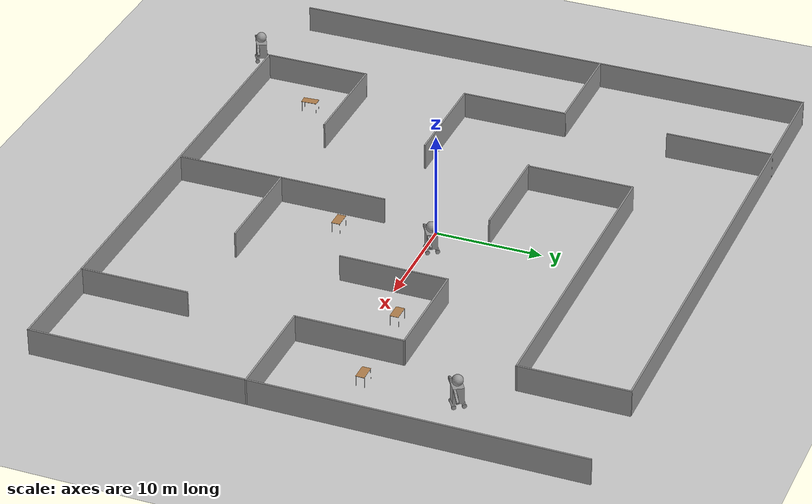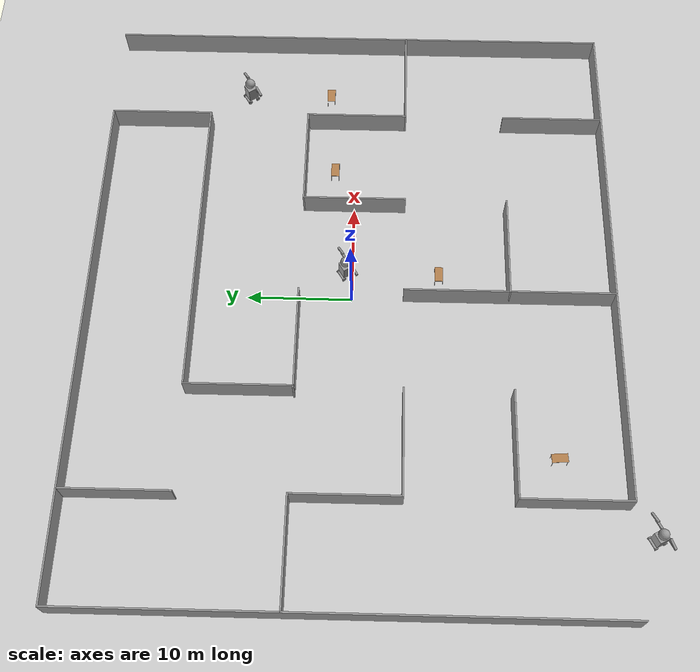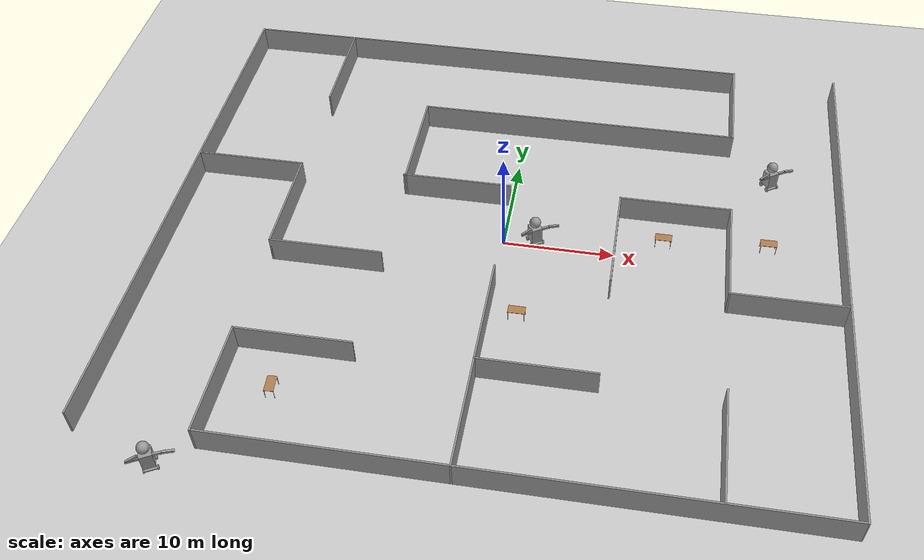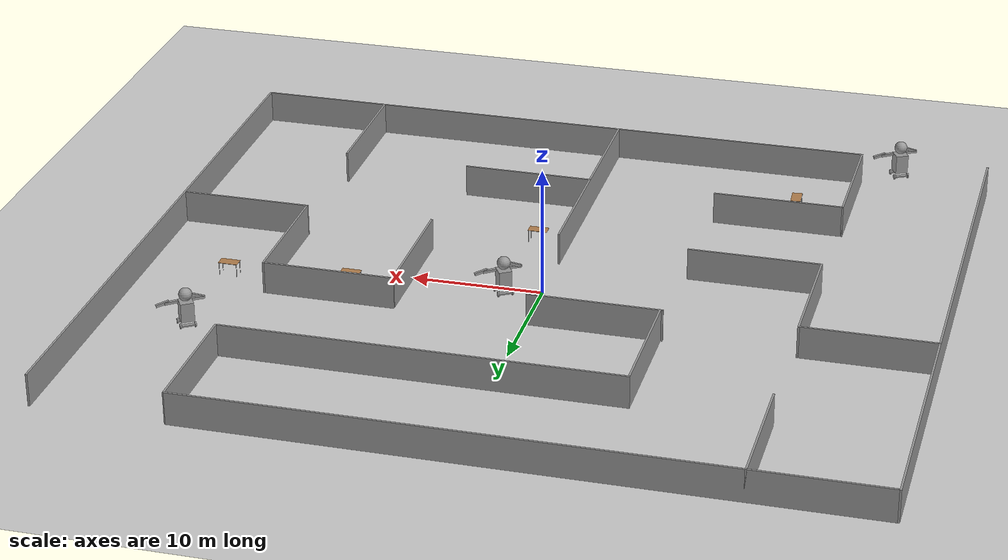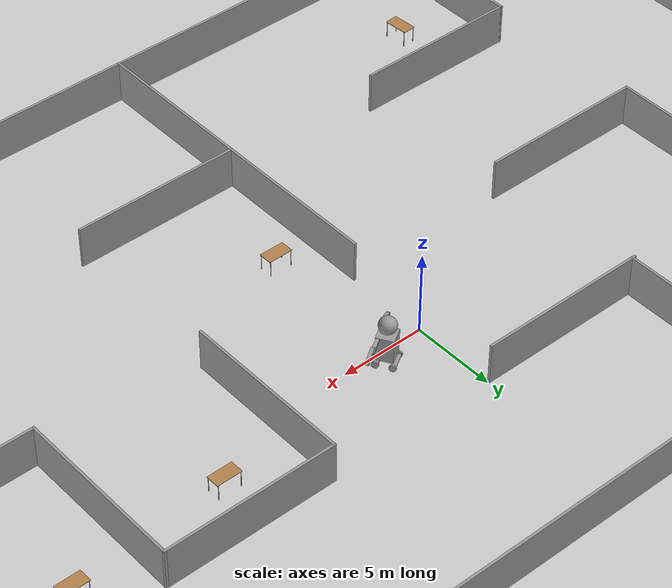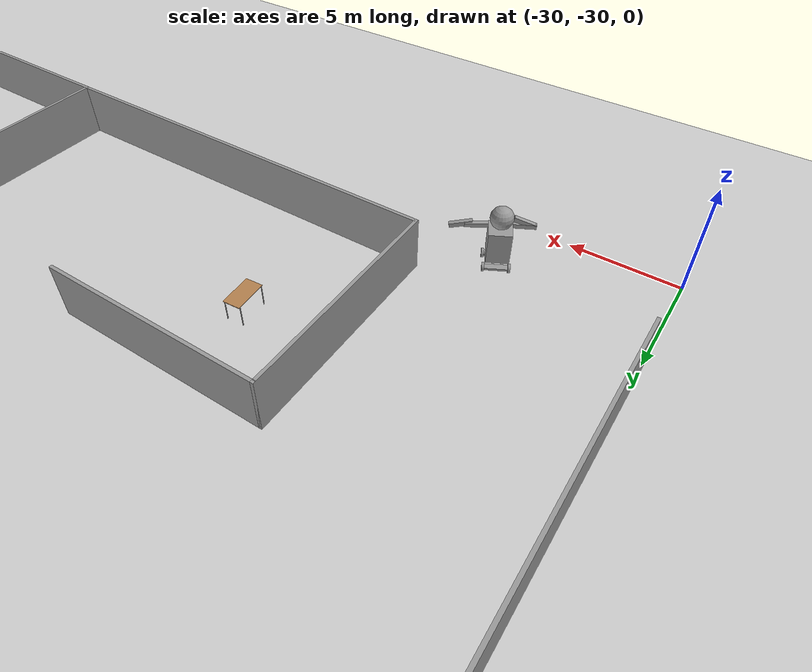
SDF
<sdf version="1.7">
 <world name="default">
  <plugin name="welcome_message" filename="libwelcome_message.so"/>
  <light name="sun" type="directional">
   <pose>0 0 10 0 -0 0</pose>
   <diffuse>0.8 0.8 0.8 1</diffuse>
   <specular>0.2 0.2 0.2 1</specular>
   <attenuation>
    <range>1000</range>
    <constant>0.9</constant>
    <linear>0.01</linear>
    <quadratic>0.001</quadratic>
   </attenuation>
   <direction>-0.5 0.1 -0.9</direction>
   <spot><inner_angle>0</inner_angle><outer_angle>0</outer_angle><falloff>0</falloff></spot>
  </light>
  <model name="ground_plane">
   <static>1</static>
   <link name="link">
    <collision name="collision">
     <geometry><plane><normal>0 0 1</normal><size>100 100</size></plane></geometry>
     <surface>
      <contact><collide_bitmask>65535</collide_bitmask></contact>
      <friction><ode><mu>100</mu><mu2>50</mu2></ode></friction>
     </surface>
    </collision>
    <visual name="visual">
     <cast_shadows>0</cast_shadows>
     <geometry><plane><normal>0 0 1</normal><size>100 100</size></plane></geometry>
     <material>
      <script><uri>file://media/materials/scripts/gazebo.material</uri><name>Gazebo/Grey</name></script>
     </material>
    </visual>
   </link>
  </model>
  <gravity>0 0 -9.8</gravity>
  <magnetic_field>6e-06 2.3e-05 -4.2e-05</magnetic_field>
  <atmosphere type="adiabatic"/>
  <physics type="ode">
   <max_step_size>0.001</max_step_size>
   <real_time_factor>1</real_time_factor>
   <real_time_update_rate>1000</real_time_update_rate>
  </physics>
  <scene><ambient>0.4 0.4 0.4 1</ambient><background>0.7 0.7 0.7 1</background><shadows>1</shadows></scene>
  <spherical_coordinates>
   <surface_model>EARTH_WGS84</surface_model>
   <latitude_deg>0</latitude_deg>
   <longitude_deg>0</longitude_deg>
   <elevation>0</elevation>
   <heading_deg>0</heading_deg>
  </spherical_coordinates>
  <model name="maze">
   <link name="Wall_0">
    <pose>-30 0 0 0 -0 1.5708</pose>
    <visual name="Wall_0_Visual">
     <pose>0 0 1.25 0 -0 0</pose>
     <geometry><box><size>50.15 0.15 2.5</size></box></geometry>
     <material>
      <script><uri>file://media/materials/scripts/gazebo.material</uri><name>Gazebo/Grey</name></script>
      <ambient>1 1 1 1</ambient>
      <shader type="pixel"/>
     </material>
     <meta><layer>0</layer></meta>
    </visual>
    <collision name="Wall_0_Collision">
     <pose>0 0 1.25 0 -0 0</pose>
     <geometry><box><size>50.15 0.15 2.5</size></box></geometry>
     <surface>
      <friction>
       <ode><mu>1</mu><mu2>1</mu2><fdir1>0 0 0</fdir1><slip1>0</slip1><slip2>0</slip2></ode>
       <torsional>
        <coefficient>1</coefficient>
        <patch_radius>0</patch_radius>
        <surface_radius>0</surface_radius>
        <use_patch_radius>1</use_patch_radius>
        <ode><slip>0</slip></ode>
       </torsional>
      </friction>
      <bounce><restitution_coefficient>0</restitution_coefficient><threshold>1e+06</threshold></bounce>
      <contact>
       <collide_without_contact>0</collide_without_contact>
       <collide_without_contact_bitmask>1</collide_without_contact_bitmask>
       <collide_bitmask>1</collide_bitmask>
       <ode>
        <soft_cfm>0</soft_cfm>
        <soft_erp>0.2</soft_erp>
        <kp>1e+13</kp>
        <kd>1</kd>
        <max_vel>0.01</max_vel>
        <min_depth>0</min_depth>
       </ode>
       <bullet>
        <split_impulse>1</split_impulse>
        <split_impulse_penetration_threshold>-0.01</split_impulse_penetration_threshold>
        <soft_cfm>0</soft_cfm>
        <soft_erp>0.2</soft_erp>
        <kp>1e+13</kp>
        <kd>1</kd>
       </bullet>
      </contact>
     </surface>
    </collision>
   </link>
   <link name="Wall_1">
    <pose>-5 25 0 0 -0 0</pose>
    <inertial>
     <mass>1</mass>
     <inertia><ixx>1</ixx><ixy>0</ixy><ixz>0</ixz><iyy>1</iyy><iyz>0</iyz><izz>1</izz></inertia>
    </inertial>
    <visual name="Wall_1_Visual">
     <pose>0 0 1.25 0 -0 0</pose>
     <geometry><box><size>50 0.15 2.5</size></box></geometry>
     <material>
      <script><uri>file://media/materials/scripts/gazebo.material</uri><name>Gazebo/Grey</name></script>
      <ambient>1 1 1 1</ambient>
      <shader type="pixel"><normal_map>__default__</normal_map></shader>
      <diffuse>0.7 0.7 0.7 1</diffuse>
      <specular>0.01 0.01 0.01 1</specular>
      <emissive>0 0 0 1</emissive>
     </material>
     <meta><layer>0</layer></meta>
    </visual>
    <collision name="Wall_1_Collision">
     <pose>0 0 1.25 0 -0 0</pose>
     <geometry><box><size>50 0.15 2.5</size></box></geometry>
     <surface>
      <friction>
       <ode><mu>1</mu><mu2>1</mu2><fdir1>0 0 0</fdir1><slip1>0</slip1><slip2>0</slip2></ode>
       <torsional>
        <coefficient>1</coefficient>
        <patch_radius>0</patch_radius>
        <surface_radius>0</surface_radius>
        <use_patch_radius>1</use_patch_radius>
        <ode><slip>0</slip></ode>
       </torsional>
      </friction>
      <bounce><restitution_coefficient>0</restitution_coefficient><threshold>1e+06</threshold></bounce>
      <contact>
       <collide_without_contact>0</collide_without_contact>
       <collide_without_contact_bitmask>1</collide_without_contact_bitmask>
       <collide_bitmask>1</collide_bitmask>
       <ode>
        <soft_cfm>0</soft_cfm>
        <soft_erp>0.2</soft_erp>
        <kp>1e+13</kp>
        <kd>1</kd>
        <max_vel>0.01</max_vel>
        <min_depth>0</min_depth>
       </ode>
       <bullet>
        <split_impulse>1</split_impulse>
        <split_impulse_penetration_threshold>-0.01</split_impulse_penetration_threshold>
        <soft_cfm>0</soft_cfm>
        <soft_erp>0.2</soft_erp>
        <kp>1e+13</kp>
        <kd>1</kd>
       </bullet>
      </contact>
     </surface>
    </collision>
   </link>
   <link name="Wall_10">
    <pose>-25 5 0 0 -0 0</pose>
    <visual name="Wall_10_Visual">
     <pose>0 0 1.25 0 -0 0</pose>
     <geometry><box><size>10.15 0.15 2.5</size></box></geometry>
     <material>
      <script><uri>file://media/materials/scripts/gazebo.material</uri><name>Gazebo/Grey</name></script>
      <ambient>1 1 1 1</ambient>
      <shader type="pixel"/>
     </material>
     <meta><layer>0</layer></meta>
    </visual>
    <collision name="Wall_10_Collision">
     <pose>0 0 1.25 0 -0 0</pose>
     <geometry><box><size>10.15 0.15 2.5</size></box></geometry>
     <surface>
      <friction>
       <ode><mu>1</mu><mu2>1</mu2><fdir1>0 0 0</fdir1><slip1>0</slip1><slip2>0</slip2></ode>
       <torsional>
        <coefficient>1</coefficient>
        <patch_radius>0</patch_radius>
        <surface_radius>0</surface_radius>
        <use_patch_radius>1</use_patch_radius>
        <ode><slip>0</slip></ode>
       </torsional>
      </friction>
      <bounce><restitution_coefficient>0</restitution_coefficient><threshold>1e+06</threshold></bounce>
      <contact>
       <collide_without_contact>0</collide_without_contact>
       <collide_without_contact_bitmask>1</collide_without_contact_bitmask>
       <collide_bitmask>1</collide_bitmask>
       <ode>
        <soft_cfm>0</soft_cfm>
        <soft_erp>0.2</soft_erp>
        <kp>1e+13</kp>
        <kd>1</kd>
        <max_vel>0.01</max_vel>
        <min_depth>0</min_depth>
       </ode>
       <bullet>
        <split_impulse>1</split_impulse>
        <split_impulse_penetration_threshold>-0.01</split_impulse_penetration_threshold>
        <soft_cfm>0</soft_cfm>
        <soft_erp>0.2</soft_erp>
        <kp>1e+13</kp>
        <kd>1</kd>
       </bullet>
      </contact>
     </surface>
    </collision>
   </link>
   <link name="Wall_13">
    <pose>-20 0 0 0 0 -1.5708</pose>
    <visual name="Wall_13_Visual">
     <pose>0 0 1.25 0 -0 0</pose>
     <geometry><box><size>10.15 0.15 2.5</size></box></geometry>
     <material>
      <script><uri>file://media/materials/scripts/gazebo.material</uri><name>Gazebo/Grey</name></script>
      <ambient>1 1 1 1</ambient>
      <shader type="pixel"/>
     </material>
     <meta><layer>0</layer></meta>
    </visual>
    <collision name="Wall_13_Collision">
     <pose>0 0 1.25 0 -0 0</pose>
     <geometry><box><size>10.15 0.15 2.5</size></box></geometry>
     <surface>
      <friction>
       <ode><mu>1</mu><mu2>1</mu2><fdir1>0 0 0</fdir1><slip1>0</slip1><slip2>0</slip2></ode>
       <torsional>
        <coefficient>1</coefficient>
        <patch_radius>0</patch_radius>
        <surface_radius>0</surface_radius>
        <use_patch_radius>1</use_patch_radius>
        <ode><slip>0</slip></ode>
       </torsional>
      </friction>
      <bounce><restitution_coefficient>0</restitution_coefficient><threshold>1e+06</threshold></bounce>
      <contact>
       <collide_without_contact>0</collide_without_contact>
       <collide_without_contact_bitmask>1</collide_without_contact_bitmask>
       <collide_bitmask>1</collide_bitmask>
       <ode>
        <soft_cfm>0</soft_cfm>
        <soft_erp>0.2</soft_erp>
        <kp>1e+13</kp>
        <kd>1</kd>
        <max_vel>0.01</max_vel>
        <min_depth>0</min_depth>
       </ode>
       <bullet>
        <split_impulse>1</split_impulse>
        <split_impulse_penetration_threshold>-0.01</split_impulse_penetration_threshold>
        <soft_cfm>0</soft_cfm>
        <soft_erp>0.2</soft_erp>
        <kp>1e+13</kp>
        <kd>1</kd>
       </bullet>
      </contact>
     </surface>
    </collision>
   </link>
   <link name="Wall_15">
    <pose>-15 -5 0 0 -0 0</pose>
    <visual name="Wall_15_Visual">
     <pose>0 0 1.25 0 -0 0</pose>
     <geometry><box><size>10.15 0.15 2.5</size></box></geometry>
     <material>
      <script><uri>file://media/materials/scripts/gazebo.material</uri><name>Gazebo/Grey</name></script>
      <ambient>1 1 1 1</ambient>
      <shader type="pixel"/>
     </material>
     <meta><layer>0</layer></meta>
    </visual>
    <collision name="Wall_15_Collision">
     <pose>0 0 1.25 0 -0 0</pose>
     <geometry><box><size>10.15 0.15 2.5</size></box></geometry>
     <surface>
      <friction>
       <ode><mu>1</mu><mu2>1</mu2><fdir1>0 0 0</fdir1><slip1>0</slip1><slip2>0</slip2></ode>
       <torsional>
        <coefficient>1</coefficient>
        <patch_radius>0</patch_radius>
        <surface_radius>0</surface_radius>
        <use_patch_radius>1</use_patch_radius>
        <ode><slip>0</slip></ode>
       </torsional>
      </friction>
      <bounce><restitution_coefficient>0</restitution_coefficient><threshold>1e+06</threshold></bounce>
      <contact>
       <collide_without_contact>0</collide_without_contact>
       <collide_without_contact_bitmask>1</collide_without_contact_bitmask>
       <collide_bitmask>1</collide_bitmask>
       <ode>
        <soft_cfm>0</soft_cfm>
        <soft_erp>0.2</soft_erp>
        <kp>1e+13</kp>
        <kd>1</kd>
        <max_vel>0.01</max_vel>
        <min_depth>0</min_depth>
       </ode>
       <bullet>
        <split_impulse>1</split_impulse>
        <split_impulse_penetration_threshold>-0.01</split_impulse_penetration_threshold>
        <soft_cfm>0</soft_cfm>
        <soft_erp>0.2</soft_erp>
        <kp>1e+13</kp>
        <kd>1</kd>
       </bullet>
      </contact>
     </surface>
    </collision>
   </link>
   <link name="Wall_17">
    <pose>-20 20 0 0 0 -1.5708</pose>
    <visual name="Wall_17_Visual">
     <pose>0 0 1.25 0 -0 0</pose>
     <geometry><box><size>10.15 0.15 2.5</size></box></geometry>
     <material>
      <script><uri>file://media/materials/scripts/gazebo.material</uri><name>Gazebo/Grey</name></script>
      <ambient>1 1 1 1</ambient>
      <shader type="pixel"/>
     </material>
     <meta><layer>0</layer></meta>
    </visual>
    <collision name="Wall_17_Collision">
     <pose>0 0 1.25 0 -0 0</pose>
     <geometry><box><size>10.15 0.15 2.5</size></box></geometry>
     <surface>
      <friction>
       <ode><mu>1</mu><mu2>1</mu2><fdir1>0 0 0</fdir1><slip1>0</slip1><slip2>0</slip2></ode>
       <torsional>
        <coefficient>1</coefficient>
        <patch_radius>0</patch_radius>
        <surface_radius>0</surface_radius>
        <use_patch_radius>1</use_patch_radius>
        <ode><slip>0</slip></ode>
       </torsional>
      </friction>
      <bounce><restitution_coefficient>0</restitution_coefficient><threshold>1e+06</threshold></bounce>
      <contact>
       <collide_without_contact>0</collide_without_contact>
       <collide_without_contact_bitmask>1</collide_without_contact_bitmask>
       <collide_bitmask>1</collide_bitmask>
       <ode>
        <soft_cfm>0</soft_cfm>
        <soft_erp>0.2</soft_erp>
        <kp>1e+13</kp>
        <kd>1</kd>
        <max_vel>0.01</max_vel>
        <min_depth>0</min_depth>
       </ode>
       <bullet>
        <split_impulse>1</split_impulse>
        <split_impulse_penetration_threshold>-0.01</split_impulse_penetration_threshold>
        <soft_cfm>0</soft_cfm>
        <soft_erp>0.2</soft_erp>
        <kp>1e+13</kp>
        <kd>1</kd>
       </bullet>
      </contact>
     </surface>
    </collision>
   </link>
   <link name="Wall_19">
    <pose>-1e-06 -15 0 0 -0 1.5708</pose>
    <visual name="Wall_19_Visual">
     <pose>0 0 1.25 0 -0 0</pose>
     <geometry><box><size>20.15 0.15 2.5</size></box></geometry>
     <material>
      <script><uri>file://media/materials/scripts/gazebo.material</uri><name>Gazebo/Grey</name></script>
      <ambient>1 1 1 1</ambient>
      <shader type="pixel"/>
     </material>
     <meta><layer>0</layer></meta>
    </visual>
    <collision name="Wall_19_Collision">
     <pose>0 0 1.25 0 -0 0</pose>
     <geometry><box><size>20.15 0.15 2.5</size></box></geometry>
     <surface>
      <friction>
       <ode><mu>1</mu><mu2>1</mu2><fdir1>0 0 0</fdir1><slip1>0</slip1><slip2>0</slip2></ode>
       <torsional>
        <coefficient>1</coefficient>
        <patch_radius>0</patch_radius>
        <surface_radius>0</surface_radius>
        <use_patch_radius>1</use_patch_radius>
        <ode><slip>0</slip></ode>
       </torsional>
      </friction>
      <bounce><restitution_coefficient>0</restitution_coefficient><threshold>1e+06</threshold></bounce>
      <contact>
       <collide_without_contact>0</collide_without_contact>
       <collide_without_contact_bitmask>1</collide_without_contact_bitmask>
       <collide_bitmask>1</collide_bitmask>
       <ode>
        <soft_cfm>0</soft_cfm>
        <soft_erp>0.2</soft_erp>
        <kp>1e+13</kp>
        <kd>1</kd>
        <max_vel>0.01</max_vel>
        <min_depth>0</min_depth>
       </ode>
       <bullet>
        <split_impulse>1</split_impulse>
        <split_impulse_penetration_threshold>-0.01</split_impulse_penetration_threshold>
        <soft_cfm>0</soft_cfm>
        <soft_erp>0.2</soft_erp>
        <kp>1e+13</kp>
        <kd>1</kd>
       </bullet>
      </contact>
     </surface>
    </collision>
   </link>
   <link name="Wall_2">
    <pose>30 0 0 0 0 -1.5708</pose>
    <visual name="Wall_2_Visual">
     <pose>0 0 1.25 0 -0 0</pose>
     <geometry><box><size>50.15 0.15 2.5</size></box></geometry>
     <material>
      <script><uri>file://media/materials/scripts/gazebo.material</uri><name>Gazebo/Grey</name></script>
      <ambient>1 1 1 1</ambient>
      <shader type="pixel"/>
     </material>
     <meta><layer>0</layer></meta>
    </visual>
    <collision name="Wall_2_Collision">
     <pose>0 0 1.25 0 -0 0</pose>
     <geometry><box><size>50.15 0.15 2.5</size></box></geometry>
     <surface>
      <friction>
       <ode><mu>1</mu><mu2>1</mu2><fdir1>0 0 0</fdir1><slip1>0</slip1><slip2>0</slip2></ode>
       <torsional>
        <coefficient>1</coefficient>
        <patch_radius>0</patch_radius>
        <surface_radius>0</surface_radius>
        <use_patch_radius>1</use_patch_radius>
        <ode><slip>0</slip></ode>
       </torsional>
      </friction>
      <bounce><restitution_coefficient>0</restitution_coefficient><threshold>1e+06</threshold></bounce>
      <contact>
       <collide_without_contact>0</collide_without_contact>
       <collide_without_contact_bitmask>1</collide_without_contact_bitmask>
       <collide_bitmask>1</collide_bitmask>
       <ode>
        <soft_cfm>0</soft_cfm>
        <soft_erp>0.2</soft_erp>
        <kp>1e+13</kp>
        <kd>1</kd>
        <max_vel>0.01</max_vel>
        <min_depth>0</min_depth>
       </ode>
       <bullet>
        <split_impulse>1</split_impulse>
        <split_impulse_penetration_threshold>-0.01</split_impulse_penetration_threshold>
        <soft_cfm>0</soft_cfm>
        <soft_erp>0.2</soft_erp>
        <kp>1e+13</kp>
        <kd>1</kd>
       </bullet>
      </contact>
     </surface>
    </collision>
   </link>
   <link name="Wall_21">
    <pose>20 -20 0 0 -0 1.5708</pose>
    <visual name="Wall_21_Visual">
     <pose>0 0 1.25 0 -0 0</pose>
     <geometry><box><size>10.15 0.15 2.5</size></box></geometry>
     <material>
      <script><uri>file://media/materials/scripts/gazebo.material</uri><name>Gazebo/Grey</name></script>
      <ambient>1 1 1 1</ambient>
      <shader type="pixel"/>
     </material>
     <meta><layer>0</layer></meta>
    </visual>
    <collision name="Wall_21_Collision">
     <pose>0 0 1.25 0 -0 0</pose>
     <geometry><box><size>10.15 0.15 2.5</size></box></geometry>
     <surface>
      <friction>
       <ode><mu>1</mu><mu2>1</mu2><fdir1>0 0 0</fdir1><slip1>0</slip1><slip2>0</slip2></ode>
       <torsional>
        <coefficient>1</coefficient>
        <patch_radius>0</patch_radius>
        <surface_radius>0</surface_radius>
        <use_patch_radius>1</use_patch_radius>
        <ode><slip>0</slip></ode>
       </torsional>
      </friction>
      <bounce><restitution_coefficient>0</restitution_coefficient><threshold>1e+06</threshold></bounce>
      <contact>
       <collide_without_contact>0</collide_without_contact>
       <collide_without_contact_bitmask>1</collide_without_contact_bitmask>
       <collide_bitmask>1</collide_bitmask>
       <ode>
        <soft_cfm>0</soft_cfm>
        <soft_erp>0.2</soft_erp>
        <kp>1e+13</kp>
        <kd>1</kd>
        <max_vel>0.01</max_vel>
        <min_depth>0</min_depth>
       </ode>
       <bullet>
        <split_impulse>1</split_impulse>
        <split_impulse_penetration_threshold>-0.01</split_impulse_penetration_threshold>
        <soft_cfm>0</soft_cfm>
        <soft_erp>0.2</soft_erp>
        <kp>1e+13</kp>
        <kd>1</kd>
       </bullet>
      </contact>
     </surface>
    </collision>
   </link>
   <link name="Wall_23">
    <pose>10 0 0 0 0 -1.5708</pose>
    <visual name="Wall_23_Visual">
     <pose>0 0 1.25 0 -0 0</pose>
     <geometry><box><size>10.15 0.15 2.5</size></box></geometry>
     <material>
      <script><uri>file://media/materials/scripts/gazebo.material</uri><name>Gazebo/Grey</name></script>
      <ambient>1 1 1 1</ambient>
      <shader type="pixel"/>
     </material>
     <meta><layer>0</layer></meta>
    </visual>
    <collision name="Wall_23_Collision">
     <pose>0 0 1.25 0 -0 0</pose>
     <geometry><box><size>10.15 0.15 2.5</size></box></geometry>
     <surface>
      <friction>
       <ode><mu>1</mu><mu2>1</mu2><fdir1>0 0 0</fdir1><slip1>0</slip1><slip2>0</slip2></ode>
       <torsional>
        <coefficient>1</coefficient>
        <patch_radius>0</patch_radius>
        <surface_radius>0</surface_radius>
        <use_patch_radius>1</use_patch_radius>
        <ode><slip>0</slip></ode>
       </torsional>
      </friction>
      <bounce><restitution_coefficient>0</restitution_coefficient><threshold>1e+06</threshold></bounce>
      <contact>
       <collide_without_contact>0</collide_without_contact>
       <collide_without_contact_bitmask>1</collide_without_contact_bitmask>
       <collide_bitmask>1</collide_bitmask>
       <ode>
        <soft_cfm>0</soft_cfm>
        <soft_erp>0.2</soft_erp>
        <kp>1e+13</kp>
        <kd>1</kd>
        <max_vel>0.01</max_vel>
        <min_depth>0</min_depth>
       </ode>
       <bullet>
        <split_impulse>1</split_impulse>
        <split_impulse_penetration_threshold>-0.01</split_impulse_penetration_threshold>
        <soft_cfm>0</soft_cfm>
        <soft_erp>0.2</soft_erp>
        <kp>1e+13</kp>
        <kd>1</kd>
       </bullet>
      </contact>
     </surface>
    </collision>
   </link>
   <link name="Wall_25">
    <pose>5 -15 0 0 -0 0</pose>
    <visual name="Wall_25_Visual">
     <pose>0 0 1.25 0 -0 0</pose>
     <geometry><box><size>10.15 0.15 2.5</size></box></geometry>
     <material>
      <script><uri>file://media/materials/scripts/gazebo.material</uri><name>Gazebo/Grey</name></script>
      <ambient>1 1 1 1</ambient>
      <shader type="pixel"/>
     </material>
     <meta><layer>0</layer></meta>
    </visual>
    <collision name="Wall_25_Collision">
     <pose>0 0 1.25 0 -0 0</pose>
     <geometry><box><size>10.15 0.15 2.5</size></box></geometry>
     <surface>
      <friction>
       <ode><mu>1</mu><mu2>1</mu2><fdir1>0 0 0</fdir1><slip1>0</slip1><slip2>0</slip2></ode>
       <torsional>
        <coefficient>1</coefficient>
        <patch_radius>0</patch_radius>
        <surface_radius>0</surface_radius>
        <use_patch_radius>1</use_patch_radius>
        <ode><slip>0</slip></ode>
       </torsional>
      </friction>
      <bounce><restitution_coefficient>0</restitution_coefficient><threshold>1e+06</threshold></bounce>
      <contact>
       <collide_without_contact>0</collide_without_contact>
       <collide_without_contact_bitmask>1</collide_without_contact_bitmask>
       <collide_bitmask>1</collide_bitmask>
       <ode>
        <soft_cfm>0</soft_cfm>
        <soft_erp>0.2</soft_erp>
        <kp>1e+13</kp>
        <kd>1</kd>
        <max_vel>0.01</max_vel>
        <min_depth>0</min_depth>
       </ode>
       <bullet>
        <split_impulse>1</split_impulse>
        <split_impulse_penetration_threshold>-0.01</split_impulse_penetration_threshold>
        <soft_cfm>0</soft_cfm>
        <soft_erp>0.2</soft_erp>
        <kp>1e+13</kp>
        <kd>1</kd>
       </bullet>
      </contact>
     </surface>
    </collision>
   </link>
   <link name="Wall_27">
    <pose>15 5 0 0 -0 3.14159</pose>
    <visual name="Wall_27_Visual">
     <pose>0 0 1.25 0 -0 0</pose>
     <geometry><box><size>10.15 0.15 2.5</size></box></geometry>
     <material>
      <script><uri>file://media/materials/scripts/gazebo.material</uri><name>Gazebo/Grey</name></script>
      <ambient>1 1 1 1</ambient>
      <shader type="pixel"/>
     </material>
     <meta><layer>0</layer></meta>
    </visual>
    <collision name="Wall_27_Collision">
     <pose>0 0 1.25 0 -0 0</pose>
     <geometry><box><size>10.15 0.15 2.5</size></box></geometry>
     <surface>
      <friction>
       <ode><mu>1</mu><mu2>1</mu2><fdir1>0 0 0</fdir1><slip1>0</slip1><slip2>0</slip2></ode>
       <torsional>
        <coefficient>1</coefficient>
        <patch_radius>0</patch_radius>
        <surface_radius>0</surface_radius>
        <use_patch_radius>1</use_patch_radius>
        <ode><slip>0</slip></ode>
       </torsional>
      </friction>
      <bounce><restitution_coefficient>0</restitution_coefficient><threshold>1e+06</threshold></bounce>
      <contact>
       <collide_without_contact>0</collide_without_contact>
       <collide_without_contact_bitmask>1</collide_without_contact_bitmask>
       <collide_bitmask>1</collide_bitmask>
       <ode>
        <soft_cfm>0</soft_cfm>
        <soft_erp>0.2</soft_erp>
        <kp>1e+13</kp>
        <kd>1</kd>
        <max_vel>0.01</max_vel>
        <min_depth>0</min_depth>
       </ode>
       <bullet>
        <split_impulse>1</split_impulse>
        <split_impulse_penetration_threshold>-0.01</split_impulse_penetration_threshold>
        <soft_cfm>0</soft_cfm>
        <soft_erp>0.2</soft_erp>
        <kp>1e+13</kp>
        <kd>1</kd>
       </bullet>
      </contact>
     </surface>
    </collision>
   </link>
   <link name="Wall_29">
    <pose>20 0 0 0 -0 1.5708</pose>
    <visual name="Wall_29_Visual">
     <pose>0 0 1.25 0 -0 0</pose>
     <geometry><box><size>10.15 0.15 2.5</size></box></geometry>
     <material>
      <script><uri>file://media/materials/scripts/gazebo.material</uri><name>Gazebo/Grey</name></script>
      <ambient>1 1 1 1</ambient>
      <shader type="pixel"/>
     </material>
     <meta><layer>0</layer></meta>
    </visual>
    <collision name="Wall_29_Collision">
     <pose>0 0 1.25 0 -0 0</pose>
     <geometry><box><size>10.15 0.15 2.5</size></box></geometry>
     <surface>
      <friction>
       <ode><mu>1</mu><mu2>1</mu2><fdir1>0 0 0</fdir1><slip1>0</slip1><slip2>0</slip2></ode>
       <torsional>
        <coefficient>1</coefficient>
        <patch_radius>0</patch_radius>
        <surface_radius>0</surface_radius>
        <use_patch_radius>1</use_patch_radius>
        <ode><slip>0</slip></ode>
       </torsional>
      </friction>
      <bounce><restitution_coefficient>0</restitution_coefficient><threshold>1e+06</threshold></bounce>
      <contact>
       <collide_without_contact>0</collide_without_contact>
       <collide_without_contact_bitmask>1</collide_without_contact_bitmask>
       <collide_bitmask>1</collide_bitmask>
       <ode>
        <soft_cfm>0</soft_cfm>
        <soft_erp>0.2</soft_erp>
        <kp>1e+13</kp>
        <kd>1</kd>
        <max_vel>0.01</max_vel>
        <min_depth>0</min_depth>
       </ode>
       <bullet>
        <split_impulse>1</split_impulse>
        <split_impulse_penetration_threshold>-0.01</split_impulse_penetration_threshold>
        <soft_cfm>0</soft_cfm>
        <soft_erp>0.2</soft_erp>
        <kp>1e+13</kp>
        <kd>1</kd>
       </bullet>
      </contact>
     </surface>
    </collision>
   </link>
   <link name="Wall_3">
    <pose>5 -25 0 0 -0 3.14159</pose>
    <inertial>
     <mass>1</mass>
     <inertia><ixx>1</ixx><ixy>0</ixy><ixz>0</ixz><iyy>1</iyy><iyz>0</iyz><izz>1</izz></inertia>
    </inertial>
    <visual name="Wall_3_Visual">
     <pose>0 0 1.25 0 -0 0</pose>
     <geometry><box><size>50 0.15 2.5</size></box></geometry>
     <material>
      <script><uri>file://media/materials/scripts/gazebo.material</uri><name>Gazebo/Grey</name></script>
      <ambient>1 1 1 1</ambient>
      <shader type="pixel"><normal_map>__default__</normal_map></shader>
      <diffuse>0.7 0.7 0.7 1</diffuse>
      <specular>0.01 0.01 0.01 1</specular>
      <emissive>0 0 0 1</emissive>
     </material>
     <meta><layer>0</layer></meta>
    </visual>
    <collision name="Wall_3_Collision">
     <pose>0 0 1.25 0 -0 0</pose>
     <geometry><box><size>50 0.15 2.5</size></box></geometry>
     <surface>
      <friction>
       <ode><mu>1</mu><mu2>1</mu2><fdir1>0 0 0</fdir1><slip1>0</slip1><slip2>0</slip2></ode>
       <torsional>
        <coefficient>1</coefficient>
        <patch_radius>0</patch_radius>
        <surface_radius>0</surface_radius>
        <use_patch_radius>1</use_patch_radius>
        <ode><slip>0</slip></ode>
       </torsional>
      </friction>
      <bounce><restitution_coefficient>0</restitution_coefficient><threshold>1e+06</threshold></bounce>
      <contact>
       <collide_without_contact>0</collide_without_contact>
       <collide_without_contact_bitmask>1</collide_without_contact_bitmask>
       <collide_bitmask>1</collide_bitmask>
       <ode>
        <soft_cfm>0</soft_cfm>
        <soft_erp>0.2</soft_erp>
        <kp>1e+13</kp>
        <kd>1</kd>
        <max_vel>0.01</max_vel>
        <min_depth>0</min_depth>
       </ode>
       <bullet>
        <split_impulse>1</split_impulse>
        <split_impulse_penetration_threshold>-0.01</split_impulse_penetration_threshold>
        <soft_cfm>0</soft_cfm>
        <soft_erp>0.2</soft_erp>
        <kp>1e+13</kp>
        <kd>1</kd>
       </bullet>
      </contact>
     </surface>
    </collision>
   </link>
   <link name="Wall_31">
    <pose>20 20 0 0 0 -1.5708</pose>
    <visual name="Wall_31_Visual">
     <pose>0 0 1.25 0 -0 0</pose>
     <geometry><box><size>10.15 0.15 2.5</size></box></geometry>
     <material>
      <script><uri>file://media/materials/scripts/gazebo.material</uri><name>Gazebo/Grey</name></script>
      <ambient>1 1 1 1</ambient>
      <shader type="pixel"/>
     </material>
     <meta><layer>0</layer></meta>
    </visual>
    <collision name="Wall_31_Collision">
     <pose>0 0 1.25 0 -0 0</pose>
     <geometry><box><size>10.15 0.15 2.5</size></box></geometry>
     <surface>
      <friction>
       <ode><mu>1</mu><mu2>1</mu2><fdir1>0 0 0</fdir1><slip1>0</slip1><slip2>0</slip2></ode>
       <torsional>
        <coefficient>1</coefficient>
        <patch_radius>0</patch_radius>
        <surface_radius>0</surface_radius>
        <use_patch_radius>1</use_patch_radius>
        <ode><slip>0</slip></ode>
       </torsional>
      </friction>
      <bounce><restitution_coefficient>0</restitution_coefficient><threshold>1e+06</threshold></bounce>
      <contact>
       <collide_without_contact>0</collide_without_contact>
       <collide_without_contact_bitmask>1</collide_without_contact_bitmask>
       <collide_bitmask>1</collide_bitmask>
       <ode>
        <soft_cfm>0</soft_cfm>
        <soft_erp>0.2</soft_erp>
        <kp>1e+13</kp>
        <kd>1</kd>
        <max_vel>0.01</max_vel>
        <min_depth>0</min_depth>
       </ode>
       <bullet>
        <split_impulse>1</split_impulse>
        <split_impulse_penetration_threshold>-0.01</split_impulse_penetration_threshold>
        <soft_cfm>0</soft_cfm>
        <soft_erp>0.2</soft_erp>
        <kp>1e+13</kp>
        <kd>1</kd>
       </bullet>
      </contact>
     </surface>
    </collision>
   </link>
   <link name="Wall_33">
    <pose>25 -5 0 0 -0 3.14159</pose>
    <visual name="Wall_33_Visual">
     <pose>0 0 1.25 0 -0 0</pose>
     <geometry><box><size>10.15 0.15 2.5</size></box></geometry>
     <material>
      <script><uri>file://media/materials/scripts/gazebo.material</uri><name>Gazebo/Grey</name></script>
      <ambient>1 1 1 1</ambient>
      <shader type="pixel"/>
     </material>
     <meta><layer>0</layer></meta>
    </visual>
    <collision name="Wall_33_Collision">
     <pose>0 0 1.25 0 -0 0</pose>
     <geometry><box><size>10.15 0.15 2.5</size></box></geometry>
     <surface>
      <friction>
       <ode><mu>1</mu><mu2>1</mu2><fdir1>0 0 0</fdir1><slip1>0</slip1><slip2>0</slip2></ode>
       <torsional>
        <coefficient>1</coefficient>
        <patch_radius>0</patch_radius>
        <surface_radius>0</surface_radius>
        <use_patch_radius>1</use_patch_radius>
        <ode><slip>0</slip></ode>
       </torsional>
      </friction>
      <bounce><restitution_coefficient>0</restitution_coefficient><threshold>1e+06</threshold></bounce>
      <contact>
       <collide_without_contact>0</collide_without_contact>
       <collide_without_contact_bitmask>1</collide_without_contact_bitmask>
       <collide_bitmask>1</collide_bitmask>
       <ode>
        <soft_cfm>0</soft_cfm>
        <soft_erp>0.2</soft_erp>
        <kp>1e+13</kp>
        <kd>1</kd>
        <max_vel>0.01</max_vel>
        <min_depth>0</min_depth>
       </ode>
       <bullet>
        <split_impulse>1</split_impulse>
        <split_impulse_penetration_threshold>-0.01</split_impulse_penetration_threshold>
        <soft_cfm>0</soft_cfm>
        <soft_erp>0.2</soft_erp>
        <kp>1e+13</kp>
        <kd>1</kd>
       </bullet>
      </contact>
     </surface>
    </collision>
   </link>
   <link name="Wall_35">
    <pose>-5.14232 5 0 0 -0 3.14159</pose>
    <visual name="Wall_35_Visual">
     <pose>0 0 1.25 0 -0 0</pose>
     <geometry><box><size>10.15 0.15 2.5</size></box></geometry>
     <material>
      <script><uri>file://media/materials/scripts/gazebo.material</uri><name>Gazebo/Grey</name></script>
      <ambient>1 1 1 1</ambient>
      <shader type="pixel"/>
     </material>
     <meta><layer>0</layer></meta>
    </visual>
    <collision name="Wall_35_Collision">
     <pose>0 0 1.25 0 -0 0</pose>
     <geometry><box><size>10.15 0.15 2.5</size></box></geometry>
     <surface>
      <friction>
       <ode><mu>1</mu><mu2>1</mu2><fdir1>0 0 0</fdir1><slip1>0</slip1><slip2>0</slip2></ode>
       <torsional>
        <coefficient>1</coefficient>
        <patch_radius>0</patch_radius>
        <surface_radius>0</surface_radius>
        <use_patch_radius>1</use_patch_radius>
        <ode><slip>0</slip></ode>
       </torsional>
      </friction>
      <bounce><restitution_coefficient>0</restitution_coefficient><threshold>1e+06</threshold></bounce>
      <contact>
       <collide_without_contact>0</collide_without_contact>
       <collide_without_contact_bitmask>1</collide_without_contact_bitmask>
       <collide_bitmask>1</collide_bitmask>
       <ode>
        <soft_cfm>0</soft_cfm>
        <soft_erp>0.2</soft_erp>
        <kp>1e+13</kp>
        <kd>1</kd>
        <max_vel>0.01</max_vel>
        <min_depth>0</min_depth>
       </ode>
       <bullet>
        <split_impulse>1</split_impulse>
        <split_impulse_penetration_threshold>-0.01</split_impulse_penetration_threshold>
        <soft_cfm>0</soft_cfm>
        <soft_erp>0.2</soft_erp>
        <kp>1e+13</kp>
        <kd>1</kd>
       </bullet>
      </contact>
     </surface>
    </collision>
   </link>
   <link name="Wall_39">
    <pose>5 15 0 0 -0 3.14159</pose>
    <visual name="Wall_39_Visual">
     <pose>0 0 1.25 0 -0 0</pose>
     <geometry><box><size>30.15 0.15 2.5</size></box></geometry>
     <material>
      <script><uri>file://media/materials/scripts/gazebo.material</uri><name>Gazebo/Grey</name></script>
      <ambient>1 1 1 1</ambient>
      <shader type="pixel"/>
     </material>
     <meta><layer>0</layer></meta>
    </visual>
    <collision name="Wall_39_Collision">
     <pose>0 0 1.25 0 -0 0</pose>
     <geometry><box><size>30.15 0.15 2.5</size></box></geometry>
     <surface>
      <friction>
       <ode><mu>1</mu><mu2>1</mu2><fdir1>0 0 0</fdir1><slip1>0</slip1><slip2>0</slip2></ode>
       <torsional>
        <coefficient>1</coefficient>
        <patch_radius>0</patch_radius>
        <surface_radius>0</surface_radius>
        <use_patch_radius>1</use_patch_radius>
        <ode><slip>0</slip></ode>
       </torsional>
      </friction>
      <bounce><restitution_coefficient>0</restitution_coefficient><threshold>1e+06</threshold></bounce>
      <contact>
       <collide_without_contact>0</collide_without_contact>
       <collide_without_contact_bitmask>1</collide_without_contact_bitmask>
       <collide_bitmask>1</collide_bitmask>
       <ode>
        <soft_cfm>0</soft_cfm>
        <soft_erp>0.2</soft_erp>
        <kp>1e+13</kp>
        <kd>1</kd>
        <max_vel>0.01</max_vel>
        <min_depth>0</min_depth>
       </ode>
       <bullet>
        <split_impulse>1</split_impulse>
        <split_impulse_penetration_threshold>-0.01</split_impulse_penetration_threshold>
        <soft_cfm>0</soft_cfm>
        <soft_erp>0.2</soft_erp>
        <kp>1e+13</kp>
        <kd>1</kd>
       </bullet>
      </contact>
     </surface>
    </collision>
   </link>
   <link name="Wall_41">
    <pose>-10 10 0 0 -0 1.5708</pose>
    <visual name="Wall_41_Visual">
     <pose>0 0 1.25 0 -0 0</pose>
     <geometry><box><size>10.15 0.15 2.5</size></box></geometry>
     <material>
      <script><uri>file://media/materials/scripts/gazebo.material</uri><name>Gazebo/Grey</name></script>
      <ambient>1 1 1 1</ambient>
      <shader type="pixel"/>
     </material>
     <meta><layer>0</layer></meta>
    </visual>
    <collision name="Wall_41_Collision">
     <pose>0 0 1.25 0 -0 0</pose>
     <geometry><box><size>10.15 0.15 2.5</size></box></geometry>
     <surface>
      <friction>
       <ode><mu>1</mu><mu2>1</mu2><fdir1>0 0 0</fdir1><slip1>0</slip1><slip2>0</slip2></ode>
       <torsional>
        <coefficient>1</coefficient>
        <patch_radius>0</patch_radius>
        <surface_radius>0</surface_radius>
        <use_patch_radius>1</use_patch_radius>
        <ode><slip>0</slip></ode>
       </torsional>
      </friction>
      <bounce><restitution_coefficient>0</restitution_coefficient><threshold>1e+06</threshold></bounce>
      <contact>
       <collide_without_contact>0</collide_without_contact>
       <collide_without_contact_bitmask>1</collide_without_contact_bitmask>
       <collide_bitmask>1</collide_bitmask>
       <ode>
        <soft_cfm>0</soft_cfm>
        <soft_erp>0.2</soft_erp>
        <kp>1e+13</kp>
        <kd>1</kd>
        <max_vel>0.01</max_vel>
        <min_depth>0</min_depth>
       </ode>
       <bullet>
        <split_impulse>1</split_impulse>
        <split_impulse_penetration_threshold>-0.01</split_impulse_penetration_threshold>
        <soft_cfm>0</soft_cfm>
        <soft_erp>0.2</soft_erp>
        <kp>1e+13</kp>
        <kd>1</kd>
       </bullet>
      </contact>
     </surface>
    </collision>
   </link>
   <link name="Wall_5">
    <pose>-20 -20 0 0 -0 1.5708</pose>
    <visual name="Wall_5_Visual">
     <pose>0 0 1.25 0 -0 0</pose>
     <geometry><box><size>10.15 0.15 2.5</size></box></geometry>
     <material>
      <script><uri>file://media/materials/scripts/gazebo.material</uri><name>Gazebo/Grey</name></script>
      <ambient>1 1 1 1</ambient>
      <shader type="pixel"/>
     </material>
     <meta><layer>0</layer></meta>
    </visual>
    <collision name="Wall_5_Collision">
     <pose>0 0 1.25 0 -0 0</pose>
     <geometry><box><size>10.15 0.15 2.5</size></box></geometry>
     <surface>
      <friction>
       <ode><mu>1</mu><mu2>1</mu2><fdir1>0 0 0</fdir1><slip1>0</slip1><slip2>0</slip2></ode>
       <torsional>
        <coefficient>1</coefficient>
        <patch_radius>0</patch_radius>
        <surface_radius>0</surface_radius>
        <use_patch_radius>1</use_patch_radius>
        <ode><slip>0</slip></ode>
       </torsional>
      </friction>
      <bounce><restitution_coefficient>0</restitution_coefficient><threshold>1e+06</threshold></bounce>
      <contact>
       <collide_without_contact>0</collide_without_contact>
       <collide_without_contact_bitmask>1</collide_without_contact_bitmask>
       <collide_bitmask>1</collide_bitmask>
       <ode>
        <soft_cfm>0</soft_cfm>
        <soft_erp>0.2</soft_erp>
        <kp>1e+13</kp>
        <kd>1</kd>
        <max_vel>0.01</max_vel>
        <min_depth>0</min_depth>
       </ode>
       <bullet>
        <split_impulse>1</split_impulse>
        <split_impulse_penetration_threshold>-0.01</split_impulse_penetration_threshold>
        <soft_cfm>0</soft_cfm>
        <soft_erp>0.2</soft_erp>
        <kp>1e+13</kp>
        <kd>1</kd>
       </bullet>
      </contact>
     </surface>
    </collision>
   </link>
   <link name="Wall_8">
    <pose>-15 -15 0 0 -0 0</pose>
    <visual name="Wall_8_Visual">
     <pose>0 0 1.25 0 -0 0</pose>
     <geometry><box><size>10.15 0.15 2.5</size></box></geometry>
     <material>
      <script><uri>file://media/materials/scripts/gazebo.material</uri><name>Gazebo/Grey</name></script>
      <ambient>1 1 1 1</ambient>
      <shader type="pixel"/>
     </material>
     <meta><layer>0</layer></meta>
    </visual>
    <collision name="Wall_8_Collision">
     <pose>0 0 1.25 0 -0 0</pose>
     <geometry><box><size>10.15 0.15 2.5</size></box></geometry>
     <surface>
      <friction>
       <ode><mu>1</mu><mu2>1</mu2><fdir1>0 0 0</fdir1><slip1>0</slip1><slip2>0</slip2></ode>
       <torsional>
        <coefficient>1</coefficient>
        <patch_radius>0</patch_radius>
        <surface_radius>0</surface_radius>
        <use_patch_radius>1</use_patch_radius>
        <ode><slip>0</slip></ode>
       </torsional>
      </friction>
      <bounce><restitution_coefficient>0</restitution_coefficient><threshold>1e+06</threshold></bounce>
      <contact>
       <collide_without_contact>0</collide_without_contact>
       <collide_without_contact_bitmask>1</collide_without_contact_bitmask>
       <collide_bitmask>1</collide_bitmask>
       <ode>
        <soft_cfm>0</soft_cfm>
        <soft_erp>0.2</soft_erp>
        <kp>1e+13</kp>
        <kd>1</kd>
        <max_vel>0.01</max_vel>
        <min_depth>0</min_depth>
       </ode>
       <bullet>
        <split_impulse>1</split_impulse>
        <split_impulse_penetration_threshold>-0.01</split_impulse_penetration_threshold>
        <soft_cfm>0</soft_cfm>
        <soft_erp>0.2</soft_erp>
        <kp>1e+13</kp>
        <kd>1</kd>
       </bullet>
      </contact>
     </surface>
    </collision>
   </link>
   <static>1</static>
   <pose>0.01023 -0.010196 0 0 -0 0</pose>
  </model>
  <model name="humanoid_robot">
   <link name="link_1">
    <inertial>
     <mass>2.10479</mass>
     <inertia>
      <ixx>0.952439</ixx>
      <ixy>0</ixy>
      <ixz>0</ixz>
      <iyy>0.952439</iyy>
      <iyz>0</iyz>
      <izz>0.350798</izz>
     </inertia>
    </inertial>
    <pose>-0.448722 -0.08924 -0.419518 0 -0 0</pose>
    <visual name="visual">
     <pose>0 0 0.2 0 -0 0</pose>
     <geometry><box><size>1 1 1.5</size></box></geometry>
     <material>
      <lighting>1</lighting>
      <script><uri>file://media/materials/scripts/gazebo.material</uri><name>Gazebo/Grey</name></script>
      <shader type="pixel"><normal_map>__default__</normal_map></shader>
      <ambient>0.3 0.3 0.3 1</ambient>
      <diffuse>0.7 0.7 0.7 1</diffuse>
      <specular>0.01 0.01 0.01 1</specular>
      <emissive>0 0 0 1</emissive>
     </material>
    </visual>
    <collision name="collision">
     <pose>0 0 0.2 0 -0 0</pose>
     <geometry><box><size>1 1 1.5</size></box></geometry>
     <surface>
      <friction>
       <ode><mu>1</mu><mu2>1</mu2><fdir1>0 0 0</fdir1><slip1>0</slip1><slip2>0</slip2></ode>
       <torsional>
        <coefficient>1</coefficient>
        <patch_radius>0</patch_radius>
        <surface_radius>0</surface_radius>
        <use_patch_radius>1</use_patch_radius>
        <ode><slip>0</slip></ode>
       </torsional>
      </friction>
      <bounce><restitution_coefficient>0</restitution_coefficient><threshold>1e+06</threshold></bounce>
      <contact>
       <collide_without_contact>0</collide_without_contact>
       <collide_without_contact_bitmask>1</collide_without_contact_bitmask>
       <collide_bitmask>1</collide_bitmask>
       <ode>
        <soft_cfm>0</soft_cfm>
        <soft_erp>0.2</soft_erp>
        <kp>1e+13</kp>
        <kd>1</kd>
        <max_vel>0.01</max_vel>
        <min_depth>0</min_depth>
       </ode>
       <bullet>
        <split_impulse>1</split_impulse>
        <split_impulse_penetration_threshold>-0.01</split_impulse_penetration_threshold>
        <soft_cfm>0</soft_cfm>
        <soft_erp>0.2</soft_erp>
        <kp>1e+13</kp>
        <kd>1</kd>
       </bullet>
      </contact>
     </surface>
    </collision>
   </link>
   <link name="link_4">
    <inertial>
     <mass>1</mass>
     <inertia><ixx>0.1</ixx><ixy>0</ixy><ixz>0</ixz><iyy>0.1</iyy><iyz>0</iyz><izz>0.1</izz></inertia>
    </inertial>
    <pose>-0.448722 -0.08924 1.08048 0 -0 0</pose>
    <visual name="visual">
     <geometry><sphere><radius>0.5</radius></sphere></geometry>
     <material>
      <lighting>1</lighting>
      <script><uri>file://media/materials/scripts/gazebo.material</uri><name>Gazebo/Grey</name></script>
      <shader type="pixel"><normal_map>__default__</normal_map></shader>
      <ambient>0.3 0.3 0.3 1</ambient>
      <diffuse>0.7 0.7 0.7 1</diffuse>
      <specular>0.01 0.01 0.01 1</specular>
      <emissive>0 0 0 1</emissive>
     </material>
    </visual>
    <collision name="collision">
     <geometry><sphere><radius>0.5</radius></sphere></geometry>
     <surface>
      <friction>
       <ode><mu>1</mu><mu2>1</mu2><fdir1>0 0 0</fdir1><slip1>0</slip1><slip2>0</slip2></ode>
       <torsional>
        <coefficient>1</coefficient>
        <patch_radius>0</patch_radius>
        <surface_radius>0</surface_radius>
        <use_patch_radius>1</use_patch_radius>
        <ode><slip>0</slip></ode>
       </torsional>
      </friction>
      <bounce><restitution_coefficient>0</restitution_coefficient><threshold>1e+06</threshold></bounce>
      <contact>
       <collide_without_contact>0</collide_without_contact>
       <collide_without_contact_bitmask>1</collide_without_contact_bitmask>
       <collide_bitmask>1</collide_bitmask>
       <ode>
        <soft_cfm>0</soft_cfm>
        <soft_erp>0.2</soft_erp>
        <kp>1e+13</kp>
        <kd>1</kd>
        <max_vel>0.01</max_vel>
        <min_depth>0</min_depth>
       </ode>
       <bullet>
        <split_impulse>1</split_impulse>
        <split_impulse_penetration_threshold>-0.01</split_impulse_penetration_threshold>
        <soft_cfm>0</soft_cfm>
        <soft_erp>0.2</soft_erp>
        <kp>1e+13</kp>
        <kd>1</kd>
       </bullet>
      </contact>
     </surface>
    </collision>
   </link>
   <link name="link_5">
    <inertial>
     <mass>1</mass>
     <inertia>
      <ixx>0.166667</ixx>
      <ixy>0</ixy>
      <ixz>0</ixz>
      <iyy>0.166667</iyy>
      <iyz>0</iyz>
      <izz>0.166667</izz>
     </inertia>
    </inertial>
    <pose>-0.088722 0.91076 0.390482 -0.06 -0.04 0</pose>
    <visual name="visual">
     <geometry><box><size>0.2 1 0.2</size></box></geometry>
     <material>
      <lighting>1</lighting>
      <script><uri>file://media/materials/scripts/gazebo.material</uri><name>Gazebo/Grey</name></script>
      <shader type="pixel"><normal_map>__default__</normal_map></shader>
      <ambient>0.3 0.3 0.3 1</ambient>
      <diffuse>0.7 0.7 0.7 1</diffuse>
      <specular>0.01 0.01 0.01 1</specular>
      <emissive>0 0 0 1</emissive>
     </material>
    </visual>
    <collision name="collision">
     <geometry><box><size>0.2 1 0.2</size></box></geometry>
     <surface>
      <friction>
       <ode><mu>1</mu><mu2>1</mu2><fdir1>0 0 0</fdir1><slip1>0</slip1><slip2>0</slip2></ode>
       <torsional>
        <coefficient>1</coefficient>
        <patch_radius>0</patch_radius>
        <surface_radius>0</surface_radius>
        <use_patch_radius>1</use_patch_radius>
        <ode><slip>0</slip></ode>
       </torsional>
      </friction>
      <bounce><restitution_coefficient>0</restitution_coefficient><threshold>1e+06</threshold></bounce>
      <contact>
       <collide_without_contact>0</collide_without_contact>
       <collide_without_contact_bitmask>1</collide_without_contact_bitmask>
       <collide_bitmask>1</collide_bitmask>
       <ode>
        <soft_cfm>0</soft_cfm>
        <soft_erp>0.2</soft_erp>
        <kp>1e+13</kp>
        <kd>1</kd>
        <max_vel>0.01</max_vel>
        <min_depth>0</min_depth>
       </ode>
       <bullet>
        <split_impulse>1</split_impulse>
        <split_impulse_penetration_threshold>-0.01</split_impulse_penetration_threshold>
        <soft_cfm>0</soft_cfm>
        <soft_erp>0.2</soft_erp>
        <kp>1e+13</kp>
        <kd>1</kd>
       </bullet>
      </contact>
     </surface>
    </collision>
   </link>
   <link name="link_5_clone">
    <inertial>
     <mass>1</mass>
     <inertia>
      <ixx>0.166667</ixx>
      <ixy>0</ixy>
      <ixz>0</ixz>
      <iyy>0.166667</iyy>
      <iyz>0</iyz>
      <izz>0.166667</izz>
     </inertia>
    </inertial>
    <pose>-0.048722 -1.08924 0.430482 0 -0 0</pose>
    <visual name="visual">
     <geometry><box><size>0.2 1 0.2</size></box></geometry>
     <material>
      <lighting>1</lighting>
      <script><uri>file://media/materials/scripts/gazebo.material</uri><name>Gazebo/Grey</name></script>
      <shader type="pixel"><normal_map>__default__</normal_map></shader>
      <ambient>0.3 0.3 0.3 1</ambient>
      <diffuse>0.7 0.7 0.7 1</diffuse>
      <specular>0.01 0.01 0.01 1</specular>
      <emissive>0 0 0 1</emissive>
     </material>
    </visual>
    <collision name="collision">
     <geometry><box><size>0.2 1 0.2</size></box></geometry>
     <surface>
      <friction>
       <ode><mu>1</mu><mu2>1</mu2><fdir1>0 0 0</fdir1><slip1>0</slip1><slip2>0</slip2></ode>
       <torsional>
        <coefficient>1</coefficient>
        <patch_radius>0</patch_radius>
        <surface_radius>0</surface_radius>
        <use_patch_radius>1</use_patch_radius>
        <ode><slip>0</slip></ode>
       </torsional>
      </friction>
      <bounce><restitution_coefficient>0</restitution_coefficient><threshold>1e+06</threshold></bounce>
      <contact>
       <collide_without_contact>0</collide_without_contact>
       <collide_without_contact_bitmask>1</collide_without_contact_bitmask>
       <collide_bitmask>1</collide_bitmask>
       <ode>
        <soft_cfm>0</soft_cfm>
        <soft_erp>0.2</soft_erp>
        <kp>1e+13</kp>
        <kd>1</kd>
        <max_vel>0.01</max_vel>
        <min_depth>0</min_depth>
       </ode>
       <bullet>
        <split_impulse>1</split_impulse>
        <split_impulse_penetration_threshold>-0.01</split_impulse_penetration_threshold>
        <soft_cfm>0</soft_cfm>
        <soft_erp>0.2</soft_erp>
        <kp>1e+13</kp>
        <kd>1</kd>
       </bullet>
      </contact>
     </surface>
    </collision>
   </link>
   <link name="link_5_clone_clone">
    <inertial>
     <mass>1</mass>
     <inertia>
      <ixx>0.166667</ixx>
      <ixy>0</ixy>
      <ixz>0</ixz>
      <iyy>0.166667</iyy>
      <iyz>0</iyz>
      <izz>0.166667</izz>
     </inertia>
    </inertial>
    <pose>-0.048722 -1.08689 0.604392 0.369688 -0 0</pose>
    <visual name="visual">
     <geometry><box><size>0.2 1 0.2</size></box></geometry>
     <material>
      <lighting>1</lighting>
      <script><uri>file://media/materials/scripts/gazebo.material</uri><name>Gazebo/Grey</name></script>
      <shader type="pixel"><normal_map>__default__</normal_map></shader>
      <ambient>0.3 0.3 0.3 1</ambient>
      <diffuse>0.7 0.7 0.7 1</diffuse>
      <specular>0.01 0.01 0.01 1</specular>
      <emissive>0 0 0 1</emissive>
     </material>
    </visual>
    <collision name="collision">
     <geometry><box><size>0.2 1 0.2</size></box></geometry>
     <surface>
      <friction>
       <ode><mu>1</mu><mu2>1</mu2><fdir1>0 0 0</fdir1><slip1>0</slip1><slip2>0</slip2></ode>
       <torsional>
        <coefficient>1</coefficient>
        <patch_radius>0</patch_radius>
        <surface_radius>0</surface_radius>
        <use_patch_radius>1</use_patch_radius>
        <ode><slip>0</slip></ode>
       </torsional>
      </friction>
      <bounce><restitution_coefficient>0</restitution_coefficient><threshold>1e+06</threshold></bounce>
      <contact>
       <collide_without_contact>0</collide_without_contact>
       <collide_without_contact_bitmask>1</collide_without_contact_bitmask>
       <collide_bitmask>1</collide_bitmask>
       <ode>
        <soft_cfm>0</soft_cfm>
        <soft_erp>0.2</soft_erp>
        <kp>1e+13</kp>
        <kd>1</kd>
        <max_vel>0.01</max_vel>
        <min_depth>0</min_depth>
       </ode>
       <bullet>
        <split_impulse>1</split_impulse>
        <split_impulse_penetration_threshold>-0.01</split_impulse_penetration_threshold>
        <soft_cfm>0</soft_cfm>
        <soft_erp>0.2</soft_erp>
        <kp>1e+13</kp>
        <kd>1</kd>
       </bullet>
      </contact>
     </surface>
    </collision>
   </link>
   <link name="link_5_clone_clone_0">
    <inertial>
     <mass>1</mass>
     <inertia>
      <ixx>0.166667</ixx>
      <ixy>0</ixy>
      <ixz>0</ixz>
      <iyy>0.166667</iyy>
      <iyz>0</iyz>
      <izz>0.166667</izz>
     </inertia>
    </inertial>
    <pose>-0.043643 1.55059 0.350025 -0.239275 0 0</pose>
    <visual name="visual">
     <geometry><box><size>0.2 1 0.2</size></box></geometry>
     <material>
      <lighting>1</lighting>
      <script><uri>file://media/materials/scripts/gazebo.material</uri><name>Gazebo/Grey</name></script>
      <shader type="pixel"><normal_map>__default__</normal_map></shader>
      <ambient>0.3 0.3 0.3 1</ambient>
      <diffuse>0.7 0.7 0.7 1</diffuse>
      <specular>0.01 0.01 0.01 1</specular>
      <emissive>0 0 0 1</emissive>
     </material>
    </visual>
    <collision name="collision">
     <geometry><box><size>0.2 1 0.2</size></box></geometry>
     <surface>
      <friction>
       <ode><mu>1</mu><mu2>1</mu2><fdir1>0 0 0</fdir1><slip1>0</slip1><slip2>0</slip2></ode>
       <torsional>
        <coefficient>1</coefficient>
        <patch_radius>0</patch_radius>
        <surface_radius>0</surface_radius>
        <use_patch_radius>1</use_patch_radius>
        <ode><slip>0</slip></ode>
       </torsional>
      </friction>
      <bounce><restitution_coefficient>0</restitution_coefficient><threshold>1e+06</threshold></bounce>
      <contact>
       <collide_without_contact>0</collide_without_contact>
       <collide_without_contact_bitmask>1</collide_without_contact_bitmask>
       <collide_bitmask>1</collide_bitmask>
       <ode>
        <soft_cfm>0</soft_cfm>
        <soft_erp>0.2</soft_erp>
        <kp>1e+13</kp>
        <kd>1</kd>
        <max_vel>0.01</max_vel>
        <min_depth>0</min_depth>
       </ode>
       <bullet>
        <split_impulse>1</split_impulse>
        <split_impulse_penetration_threshold>-0.01</split_impulse_penetration_threshold>
        <soft_cfm>0</soft_cfm>
        <soft_erp>0.2</soft_erp>
        <kp>1e+13</kp>
        <kd>1</kd>
       </bullet>
      </contact>
     </surface>
    </collision>
   </link>
   <model name="robot">
    <link name="link_1">
     <inertial>
      <mass>1</mass>
      <inertia>
       <ixx>0.166667</ixx>
       <ixy>0</ixy>
       <ixz>0</ixz>
       <iyy>0.166667</iyy>
       <iyz>0</iyz>
       <izz>0.166667</izz>
      </inertia>
     </inertial>
     <visual name="visual">
      <geometry><box><size>0.3 1 0.1</size></box></geometry>
      <material>
       <lighting>1</lighting>
       <script><uri>file://media/materials/scripts/gazebo.material</uri><name>Gazebo/Grey</name></script>
       <shader type="pixel"><normal_map>__default__</normal_map></shader>
       <ambient>0.3 0.3 0.3 1</ambient>
       <diffuse>0.7 0.7 0.7 1</diffuse>
       <specular>0.01 0.01 0.01 1</specular>
       <emissive>0 0 0 1</emissive>
      </material>
     </visual>
     <collision name="collision">
      <geometry><box><size>0.3 1 0.1</size></box></geometry>
      <surface>
       <friction>
        <ode><mu>1</mu><mu2>1</mu2><fdir1>0 0 0</fdir1><slip1>0</slip1><slip2>0</slip2></ode>
        <torsional>
         <coefficient>1</coefficient>
         <patch_radius>0</patch_radius>
         <surface_radius>0</surface_radius>
         <use_patch_radius>1</use_patch_radius>
         <ode><slip>0</slip></ode>
        </torsional>
       </friction>
       <bounce><restitution_coefficient>0</restitution_coefficient><threshold>1e+06</threshold></bounce>
       <contact>
        <collide_without_contact>0</collide_without_contact>
        <collide_without_contact_bitmask>1</collide_without_contact_bitmask>
        <collide_bitmask>1</collide_bitmask>
        <ode>
         <soft_cfm>0</soft_cfm>
         <soft_erp>0.2</soft_erp>
         <kp>1e+13</kp>
         <kd>1</kd>
         <max_vel>0.01</max_vel>
         <min_depth>0</min_depth>
        </ode>
        <bullet>
         <split_impulse>1</split_impulse>
         <split_impulse_penetration_threshold>-0.01</split_impulse_penetration_threshold>
         <soft_cfm>0</soft_cfm>
         <soft_erp>0.2</soft_erp>
         <kp>1e+13</kp>
         <kd>1</kd>
        </bullet>
       </contact>
      </surface>
     </collision>
    </link>
    <link name="link_3_clone">
     <inertial>
      <mass>1</mass>
      <inertia><ixx>0.145833</ixx><ixy>0</ixy><ixz>0</ixz><iyy>0.145833</iyy><iyz>0</iyz><izz>0.125</izz></inertia>
     </inertial>
     <pose>0 -0.550019 0 1.5707 -0 0</pose>
     <visual name="visual">
      <geometry><cylinder><radius>0.2</radius><length>0.1</length></cylinder></geometry>
      <material>
       <lighting>1</lighting>
       <script><uri>file://media/materials/scripts/gazebo.material</uri><name>Gazebo/Grey</name></script>
       <shader type="pixel"><normal_map>__default__</normal_map></shader>
       <ambient>0.3 0.3 0.3 1</ambient>
       <diffuse>0.7 0.7 0.7 1</diffuse>
       <specular>0.01 0.01 0.01 1</specular>
       <emissive>0 0 0 1</emissive>
      </material>
     </visual>
     <collision name="collision">
      <geometry><cylinder><radius>0.2</radius><length>0.1</length></cylinder></geometry>
      <surface>
       <friction>
        <ode><mu>1</mu><mu2>1</mu2><fdir1>0 0 0</fdir1><slip1>0</slip1><slip2>0</slip2></ode>
        <torsional>
         <coefficient>1</coefficient>
         <patch_radius>0</patch_radius>
         <surface_radius>0</surface_radius>
         <use_patch_radius>1</use_patch_radius>
         <ode><slip>0</slip></ode>
        </torsional>
       </friction>
       <bounce><restitution_coefficient>0</restitution_coefficient><threshold>1e+06</threshold></bounce>
       <contact>
        <collide_without_contact>0</collide_without_contact>
        <collide_without_contact_bitmask>1</collide_without_contact_bitmask>
        <collide_bitmask>1</collide_bitmask>
        <ode>
         <soft_cfm>0</soft_cfm>
         <soft_erp>0.2</soft_erp>
         <kp>1e+13</kp>
         <kd>1</kd>
         <max_vel>0.01</max_vel>
         <min_depth>0</min_depth>
        </ode>
        <bullet>
         <split_impulse>1</split_impulse>
         <split_impulse_penetration_threshold>-0.01</split_impulse_penetration_threshold>
         <soft_cfm>0</soft_cfm>
         <soft_erp>0.2</soft_erp>
         <kp>1e+13</kp>
         <kd>1</kd>
        </bullet>
       </contact>
      </surface>
     </collision>
    </link>
    <link name="link_3_clone_clone">
     <inertial>
      <mass>1</mass>
      <inertia><ixx>0.145833</ixx><ixy>0</ixy><ixz>0</ixz><iyy>0.145833</iyy><iyz>0</iyz><izz>0.125</izz></inertia>
     </inertial>
     <pose>0 0.550019 0 1.5707 -0 0</pose>
     <visual name="visual">
      <geometry><cylinder><radius>0.2</radius><length>0.1</length></cylinder></geometry>
      <material>
       <lighting>1</lighting>
       <script><uri>file://media/materials/scripts/gazebo.material</uri><name>Gazebo/Grey</name></script>
       <shader type="pixel"><normal_map>__default__</normal_map></shader>
       <ambient>0.3 0.3 0.3 1</ambient>
       <diffuse>0.7 0.7 0.7 1</diffuse>
       <specular>0.01 0.01 0.01 1</specular>
       <emissive>0 0 0 1</emissive>
      </material>
     </visual>
     <collision name="collision">
      <geometry><cylinder><radius>0.2</radius><length>0.1</length></cylinder></geometry>
      <surface>
       <friction>
        <ode><mu>1</mu><mu2>1</mu2><fdir1>0 0 0</fdir1><slip1>0</slip1><slip2>0</slip2></ode>
        <torsional>
         <coefficient>1</coefficient>
         <patch_radius>0</patch_radius>
         <surface_radius>0</surface_radius>
         <use_patch_radius>1</use_patch_radius>
         <ode><slip>0</slip></ode>
        </torsional>
       </friction>
       <bounce><restitution_coefficient>0</restitution_coefficient><threshold>1e+06</threshold></bounce>
       <contact>
        <collide_without_contact>0</collide_without_contact>
        <collide_without_contact_bitmask>1</collide_without_contact_bitmask>
        <collide_bitmask>1</collide_bitmask>
        <ode>
         <soft_cfm>0</soft_cfm>
         <soft_erp>0.2</soft_erp>
         <kp>1e+13</kp>
         <kd>1</kd>
         <max_vel>0.01</max_vel>
         <min_depth>0</min_depth>
        </ode>
        <bullet>
         <split_impulse>1</split_impulse>
         <split_impulse_penetration_threshold>-0.01</split_impulse_penetration_threshold>
         <soft_cfm>0</soft_cfm>
         <soft_erp>0.2</soft_erp>
         <kp>1e+13</kp>
         <kd>1</kd>
        </bullet>
       </contact>
      </surface>
     </collision>
    </link>
    <joint name="link_1_JOINT_1" type="revolute">
     <parent>link_1</parent>
     <child>link_3_clone</child>
     <axis>
      <xyz>0 0 1</xyz>
      <limit>
       <lower>-1.79769e+308</lower>
       <upper>1.79769e+308</upper>
       <effort>-1</effort>
       <velocity>-1</velocity>
      </limit>
      <dynamics>
       <spring_reference>0</spring_reference>
       <spring_stiffness>0</spring_stiffness>
       <damping>0</damping>
      </dynamics>
     </axis>
     <physics>
      <ode><limit><cfm>0</cfm><erp>0.2</erp></limit><suspension><cfm>0</cfm><erp>0.2</erp></suspension></ode>
     </physics>
    </joint>
    <joint name="link_1_JOINT_3" type="revolute">
     <parent>link_1</parent>
     <child>link_3_clone_clone</child>
     <axis>
      <xyz>0 0 1</xyz>
      <limit>
       <lower>-1.79769e+308</lower>
       <upper>1.79769e+308</upper>
       <effort>-1</effort>
       <velocity>-1</velocity>
      </limit>
      <dynamics>
       <spring_reference>0</spring_reference>
       <spring_stiffness>0</spring_stiffness>
       <damping>0</damping>
      </dynamics>
     </axis>
     <physics>
      <ode><limit><cfm>0</cfm><erp>0.2</erp></limit><suspension><cfm>0</cfm><erp>0.2</erp></suspension></ode>
     </physics>
    </joint>
    <static>0</static>
    <pose>-0.041176 -0.042224 -1.22566 0 -0 0</pose>
   </model>
   <model name="robot_0">
    <link name="link_1">
     <inertial>
      <mass>1</mass>
      <inertia>
       <ixx>0.166667</ixx>
       <ixy>0</ixy>
       <ixz>0</ixz>
       <iyy>0.166667</iyy>
       <iyz>0</iyz>
       <izz>0.166667</izz>
      </inertia>
     </inertial>
     <visual name="visual">
      <geometry><box><size>0.3 1 0.1</size></box></geometry>
      <material>
       <lighting>1</lighting>
       <script><uri>file://media/materials/scripts/gazebo.material</uri><name>Gazebo/Grey</name></script>
       <shader type="pixel"><normal_map>__default__</normal_map></shader>
       <ambient>0.3 0.3 0.3 1</ambient>
       <diffuse>0.7 0.7 0.7 1</diffuse>
       <specular>0.01 0.01 0.01 1</specular>
       <emissive>0 0 0 1</emissive>
      </material>
     </visual>
     <collision name="collision">
      <geometry><box><size>0.3 1 0.1</size></box></geometry>
      <surface>
       <friction>
        <ode><mu>1</mu><mu2>1</mu2><fdir1>0 0 0</fdir1><slip1>0</slip1><slip2>0</slip2></ode>
        <torsional>
         <coefficient>1</coefficient>
         <patch_radius>0</patch_radius>
         <surface_radius>0</surface_radius>
         <use_patch_radius>1</use_patch_radius>
         <ode><slip>0</slip></ode>
        </torsional>
       </friction>
       <bounce><restitution_coefficient>0</restitution_coefficient><threshold>1e+06</threshold></bounce>
       <contact>
        <collide_without_contact>0</collide_without_contact>
        <collide_without_contact_bitmask>1</collide_without_contact_bitmask>
        <collide_bitmask>1</collide_bitmask>
        <ode>
         <soft_cfm>0</soft_cfm>
         <soft_erp>0.2</soft_erp>
         <kp>1e+13</kp>
         <kd>1</kd>
         <max_vel>0.01</max_vel>
         <min_depth>0</min_depth>
        </ode>
        <bullet>
         <split_impulse>1</split_impulse>
         <split_impulse_penetration_threshold>-0.01</split_impulse_penetration_threshold>
         <soft_cfm>0</soft_cfm>
         <soft_erp>0.2</soft_erp>
         <kp>1e+13</kp>
         <kd>1</kd>
        </bullet>
       </contact>
      </surface>
     </collision>
    </link>
    <link name="link_3_clone">
     <inertial>
      <mass>1</mass>
      <inertia><ixx>0.145833</ixx><ixy>0</ixy><ixz>0</ixz><iyy>0.145833</iyy><iyz>0</iyz><izz>0.125</izz></inertia>
     </inertial>
     <pose>0 -0.550019 0 1.5707 -0 0</pose>
     <visual name="visual">
      <geometry><cylinder><radius>0.2</radius><length>0.1</length></cylinder></geometry>
      <material>
       <lighting>1</lighting>
       <script><uri>file://media/materials/scripts/gazebo.material</uri><name>Gazebo/Grey</name></script>
       <shader type="pixel"><normal_map>__default__</normal_map></shader>
       <ambient>0.3 0.3 0.3 1</ambient>
       <diffuse>0.7 0.7 0.7 1</diffuse>
       <specular>0.01 0.01 0.01 1</specular>
       <emissive>0 0 0 1</emissive>
      </material>
     </visual>
     <collision name="collision">
      <geometry><cylinder><radius>0.2</radius><length>0.1</length></cylinder></geometry>
      <surface>
       <friction>
        <ode><mu>1</mu><mu2>1</mu2><fdir1>0 0 0</fdir1><slip1>0</slip1><slip2>0</slip2></ode>
        <torsional>
         <coefficient>1</coefficient>
         <patch_radius>0</patch_radius>
         <surface_radius>0</surface_radius>
         <use_patch_radius>1</use_patch_radius>
         <ode><slip>0</slip></ode>
        </torsional>
       </friction>
       <bounce><restitution_coefficient>0</restitution_coefficient><threshold>1e+06</threshold></bounce>
       <contact>
        <collide_without_contact>0</collide_without_contact>
        <collide_without_contact_bitmask>1</collide_without_contact_bitmask>
        <collide_bitmask>1</collide_bitmask>
        <ode>
         <soft_cfm>0</soft_cfm>
         <soft_erp>0.2</soft_erp>
         <kp>1e+13</kp>
         <kd>1</kd>
         <max_vel>0.01</max_vel>
         <min_depth>0</min_depth>
        </ode>
        <bullet>
         <split_impulse>1</split_impulse>
         <split_impulse_penetration_threshold>-0.01</split_impulse_penetration_threshold>
         <soft_cfm>0</soft_cfm>
         <soft_erp>0.2</soft_erp>
         <kp>1e+13</kp>
         <kd>1</kd>
        </bullet>
       </contact>
      </surface>
     </collision>
    </link>
    <link name="link_3_clone_clone">
     <inertial>
      <mass>1</mass>
      <inertia><ixx>0.145833</ixx><ixy>0</ixy><ixz>0</ixz><iyy>0.145833</iyy><iyz>0</iyz><izz>0.125</izz></inertia>
     </inertial>
     <pose>0 0.550019 0 1.5707 -0 0</pose>
     <visual name="visual">
      <geometry><cylinder><radius>0.2</radius><length>0.1</length></cylinder></geometry>
      <material>
       <lighting>1</lighting>
       <script><uri>file://media/materials/scripts/gazebo.material</uri><name>Gazebo/Grey</name></script>
       <shader type="pixel"><normal_map>__default__</normal_map></shader>
       <ambient>0.3 0.3 0.3 1</ambient>
       <diffuse>0.7 0.7 0.7 1</diffuse>
       <specular>0.01 0.01 0.01 1</specular>
       <emissive>0 0 0 1</emissive>
      </material>
     </visual>
     <collision name="collision">
      <geometry><cylinder><radius>0.2</radius><length>0.1</length></cylinder></geometry>
      <surface>
       <friction>
        <ode><mu>1</mu><mu2>1</mu2><fdir1>0 0 0</fdir1><slip1>0</slip1><slip2>0</slip2></ode>
        <torsional>
         <coefficient>1</coefficient>
         <patch_radius>0</patch_radius>
         <surface_radius>0</surface_radius>
         <use_patch_radius>1</use_patch_radius>
         <ode><slip>0</slip></ode>
        </torsional>
       </friction>
       <bounce><restitution_coefficient>0</restitution_coefficient><threshold>1e+06</threshold></bounce>
       <contact>
        <collide_without_contact>0</collide_without_contact>
        <collide_without_contact_bitmask>1</collide_without_contact_bitmask>
        <collide_bitmask>1</collide_bitmask>
        <ode>
         <soft_cfm>0</soft_cfm>
         <soft_erp>0.2</soft_erp>
         <kp>1e+13</kp>
         <kd>1</kd>
         <max_vel>0.01</max_vel>
         <min_depth>0</min_depth>
        </ode>
        <bullet>
         <split_impulse>1</split_impulse>
         <split_impulse_penetration_threshold>-0.01</split_impulse_penetration_threshold>
         <soft_cfm>0</soft_cfm>
         <soft_erp>0.2</soft_erp>
         <kp>1e+13</kp>
         <kd>1</kd>
        </bullet>
       </contact>
      </surface>
     </collision>
    </link>
    <joint name="link_1_JOINT_1" type="revolute">
     <parent>link_1</parent>
     <child>link_3_clone</child>
     <axis>
      <xyz>0 0 1</xyz>
      <limit>
       <lower>-1.79769e+308</lower>
       <upper>1.79769e+308</upper>
       <effort>-1</effort>
       <velocity>-1</velocity>
      </limit>
      <dynamics>
       <spring_reference>0</spring_reference>
       <spring_stiffness>0</spring_stiffness>
       <damping>0</damping>
      </dynamics>
     </axis>
     <physics>
      <ode><limit><cfm>0</cfm><erp>0.2</erp></limit><suspension><cfm>0</cfm><erp>0.2</erp></suspension></ode>
     </physics>
    </joint>
    <joint name="link_1_JOINT_3" type="revolute">
     <parent>link_1</parent>
     <child>link_3_clone_clone</child>
     <axis>
      <xyz>0 0 1</xyz>
      <limit>
       <lower>-1.79769e+308</lower>
       <upper>1.79769e+308</upper>
       <effort>-1</effort>
       <velocity>-1</velocity>
      </limit>
      <dynamics>
       <spring_reference>0</spring_reference>
       <spring_stiffness>0</spring_stiffness>
       <damping>0</damping>
      </dynamics>
     </axis>
     <physics>
      <ode><limit><cfm>0</cfm><erp>0.2</erp></limit><suspension><cfm>0</cfm><erp>0.2</erp></suspension></ode>
     </physics>
    </joint>
    <static>0</static>
    <pose>-0.953654 -0.064519 -1.21068 0 -0 0</pose>
   </model>
   <joint name="link_1_JOINT_0" type="ball">
    <parent>link_1</parent>
    <child>link_4</child>
    <physics>
     <ode><limit><cfm>0</cfm><erp>0.2</erp></limit><suspension><cfm>0</cfm><erp>0.2</erp></suspension></ode>
    </physics>
   </joint>
   <joint name="link_1_JOINT_3" type="ball">
    <parent>link_1</parent>
    <child>link_5</child>
    <physics>
     <ode><limit><cfm>0</cfm><erp>0.2</erp></limit><suspension><cfm>0</cfm><erp>0.2</erp></suspension></ode>
    </physics>
   </joint>
   <joint name="link_1_JOINT_4" type="ball">
    <parent>link_1</parent>
    <child>link_5_clone</child>
    <physics>
     <ode><limit><cfm>0</cfm><erp>0.2</erp></limit><suspension><cfm>0</cfm><erp>0.2</erp></suspension></ode>
    </physics>
   </joint>
   <joint name="link_5_JOINT_10" type="revolute">
    <parent>link_5</parent>
    <child>link_5_clone_clone_0</child>
    <axis>
     <xyz>1 0 0</xyz>
     <limit>
      <lower>-1.79769e+308</lower>
      <upper>1.79769e+308</upper>
      <effort>-1</effort>
      <velocity>-1</velocity>
     </limit>
     <dynamics>
      <spring_reference>0</spring_reference>
      <spring_stiffness>0</spring_stiffness>
      <damping>0</damping>
     </dynamics>
    </axis>
    <physics>
     <ode><limit><cfm>0</cfm><erp>0.2</erp></limit><suspension><cfm>0</cfm><erp>0.2</erp></suspension></ode>
    </physics>
   </joint>
   <joint name="link_5_clone_JOINT_5" type="revolute">
    <parent>link_5_clone</parent>
    <child>link_5_clone_clone</child>
    <pose>0 0 0 -0.01 0 0</pose>
    <axis>
     <xyz>1 0 0</xyz>
     <limit>
      <lower>-1.79769e+308</lower>
      <upper>1.79769e+308</upper>
      <effort>-1</effort>
      <velocity>-1</velocity>
     </limit>
     <dynamics>
      <spring_reference>0</spring_reference>
      <spring_stiffness>0</spring_stiffness>
      <damping>0</damping>
     </dynamics>
    </axis>
    <physics>
     <ode><limit><cfm>0</cfm><erp>0.2</erp></limit><suspension><cfm>0</cfm><erp>0.2</erp></suspension></ode>
    </physics>
   </joint>
   <joint name="link_1_JOINT_1" type="fixed">
    <parent>robot::link_1</parent>
    <child>link_1</child>
    <physics>
     <ode><limit><cfm>0</cfm><erp>0.2</erp></limit><suspension><cfm>0</cfm><erp>0.2</erp></suspension></ode>
    </physics>
   </joint>
   <joint name="link_1_JOINT_2" type="fixed">
    <parent>robot_0::link_1</parent>
    <child>link_1</child>
    <physics>
     <ode><limit><cfm>0</cfm><erp>0.2</erp></limit><suspension><cfm>0</cfm><erp>0.2</erp></suspension></ode>
    </physics>
   </joint>
   <static>0</static>
   <pose>3.09578 0.286004 1.42617 -2e-06 -0.016409 -1.01995</pose>
   <scale>200 200 200</scale>
  </model>
  <model name="humanoid_robot_0">
   <link name="link_1">
    <inertial>
     <mass>2.10479</mass>
     <inertia>
      <ixx>0.952439</ixx>
      <ixy>0</ixy>
      <ixz>0</ixz>
      <iyy>0.952439</iyy>
      <iyz>0</iyz>
      <izz>0.350798</izz>
     </inertia>
    </inertial>
    <pose>-0.448722 -0.08924 -0.419518 0 -0 0</pose>
    <visual name="visual">
     <pose>0 0 0.2 0 -0 0</pose>
     <geometry><box><size>1 1 1.5</size></box></geometry>
     <material>
      <lighting>1</lighting>
      <script><uri>file://media/materials/scripts/gazebo.material</uri><name>Gazebo/Grey</name></script>
      <shader type="pixel"><normal_map>__default__</normal_map></shader>
      <ambient>0.3 0.3 0.3 1</ambient>
      <diffuse>0.7 0.7 0.7 1</diffuse>
      <specular>0.01 0.01 0.01 1</specular>
      <emissive>0 0 0 1</emissive>
     </material>
    </visual>
    <collision name="collision">
     <pose>0 0 0.2 0 -0 0</pose>
     <geometry><box><size>1 1 1.5</size></box></geometry>
     <surface>
      <friction>
       <ode><mu>1</mu><mu2>1</mu2><fdir1>0 0 0</fdir1><slip1>0</slip1><slip2>0</slip2></ode>
       <torsional>
        <coefficient>1</coefficient>
        <patch_radius>0</patch_radius>
        <surface_radius>0</surface_radius>
        <use_patch_radius>1</use_patch_radius>
        <ode><slip>0</slip></ode>
       </torsional>
      </friction>
      <bounce><restitution_coefficient>0</restitution_coefficient><threshold>1e+06</threshold></bounce>
      <contact>
       <collide_without_contact>0</collide_without_contact>
       <collide_without_contact_bitmask>1</collide_without_contact_bitmask>
       <collide_bitmask>1</collide_bitmask>
       <ode>
        <soft_cfm>0</soft_cfm>
        <soft_erp>0.2</soft_erp>
        <kp>1e+13</kp>
        <kd>1</kd>
        <max_vel>0.01</max_vel>
        <min_depth>0</min_depth>
       </ode>
       <bullet>
        <split_impulse>1</split_impulse>
        <split_impulse_penetration_threshold>-0.01</split_impulse_penetration_threshold>
        <soft_cfm>0</soft_cfm>
        <soft_erp>0.2</soft_erp>
        <kp>1e+13</kp>
        <kd>1</kd>
       </bullet>
      </contact>
     </surface>
    </collision>
   </link>
   <link name="link_4">
    <inertial>
     <mass>1</mass>
     <inertia><ixx>0.1</ixx><ixy>0</ixy><ixz>0</ixz><iyy>0.1</iyy><iyz>0</iyz><izz>0.1</izz></inertia>
    </inertial>
    <pose>-0.448722 -0.08924 1.08048 0 -0 0</pose>
    <visual name="visual">
     <geometry><sphere><radius>0.5</radius></sphere></geometry>
     <material>
      <lighting>1</lighting>
      <script><uri>file://media/materials/scripts/gazebo.material</uri><name>Gazebo/Grey</name></script>
      <shader type="pixel"><normal_map>__default__</normal_map></shader>
      <ambient>0.3 0.3 0.3 1</ambient>
      <diffuse>0.7 0.7 0.7 1</diffuse>
      <specular>0.01 0.01 0.01 1</specular>
      <emissive>0 0 0 1</emissive>
     </material>
    </visual>
    <collision name="collision">
     <geometry><sphere><radius>0.5</radius></sphere></geometry>
     <surface>
      <friction>
       <ode><mu>1</mu><mu2>1</mu2><fdir1>0 0 0</fdir1><slip1>0</slip1><slip2>0</slip2></ode>
       <torsional>
        <coefficient>1</coefficient>
        <patch_radius>0</patch_radius>
        <surface_radius>0</surface_radius>
        <use_patch_radius>1</use_patch_radius>
        <ode><slip>0</slip></ode>
       </torsional>
      </friction>
      <bounce><restitution_coefficient>0</restitution_coefficient><threshold>1e+06</threshold></bounce>
      <contact>
       <collide_without_contact>0</collide_without_contact>
       <collide_without_contact_bitmask>1</collide_without_contact_bitmask>
       <collide_bitmask>1</collide_bitmask>
       <ode>
        <soft_cfm>0</soft_cfm>
        <soft_erp>0.2</soft_erp>
        <kp>1e+13</kp>
        <kd>1</kd>
        <max_vel>0.01</max_vel>
        <min_depth>0</min_depth>
       </ode>
       <bullet>
        <split_impulse>1</split_impulse>
        <split_impulse_penetration_threshold>-0.01</split_impulse_penetration_threshold>
        <soft_cfm>0</soft_cfm>
        <soft_erp>0.2</soft_erp>
        <kp>1e+13</kp>
        <kd>1</kd>
       </bullet>
      </contact>
     </surface>
    </collision>
   </link>
   <link name="link_5">
    <inertial>
     <mass>1</mass>
     <inertia>
      <ixx>0.166667</ixx>
      <ixy>0</ixy>
      <ixz>0</ixz>
      <iyy>0.166667</iyy>
      <iyz>0</iyz>
      <izz>0.166667</izz>
     </inertia>
    </inertial>
    <pose>-0.088722 0.91076 0.390482 -0.06 -0.04 0</pose>
    <visual name="visual">
     <geometry><box><size>0.2 1 0.2</size></box></geometry>
     <material>
      <lighting>1</lighting>
      <script><uri>file://media/materials/scripts/gazebo.material</uri><name>Gazebo/Grey</name></script>
      <shader type="pixel"><normal_map>__default__</normal_map></shader>
      <ambient>0.3 0.3 0.3 1</ambient>
      <diffuse>0.7 0.7 0.7 1</diffuse>
      <specular>0.01 0.01 0.01 1</specular>
      <emissive>0 0 0 1</emissive>
     </material>
    </visual>
    <collision name="collision">
     <geometry><box><size>0.2 1 0.2</size></box></geometry>
     <surface>
      <friction>
       <ode><mu>1</mu><mu2>1</mu2><fdir1>0 0 0</fdir1><slip1>0</slip1><slip2>0</slip2></ode>
       <torsional>
        <coefficient>1</coefficient>
        <patch_radius>0</patch_radius>
        <surface_radius>0</surface_radius>
        <use_patch_radius>1</use_patch_radius>
        <ode><slip>0</slip></ode>
       </torsional>
      </friction>
      <bounce><restitution_coefficient>0</restitution_coefficient><threshold>1e+06</threshold></bounce>
      <contact>
       <collide_without_contact>0</collide_without_contact>
       <collide_without_contact_bitmask>1</collide_without_contact_bitmask>
       <collide_bitmask>1</collide_bitmask>
       <ode>
        <soft_cfm>0</soft_cfm>
        <soft_erp>0.2</soft_erp>
        <kp>1e+13</kp>
        <kd>1</kd>
        <max_vel>0.01</max_vel>
        <min_depth>0</min_depth>
       </ode>
       <bullet>
        <split_impulse>1</split_impulse>
        <split_impulse_penetration_threshold>-0.01</split_impulse_penetration_threshold>
        <soft_cfm>0</soft_cfm>
        <soft_erp>0.2</soft_erp>
        <kp>1e+13</kp>
        <kd>1</kd>
       </bullet>
      </contact>
     </surface>
    </collision>
   </link>
   <link name="link_5_clone">
    <inertial>
     <mass>1</mass>
     <inertia>
      <ixx>0.166667</ixx>
      <ixy>0</ixy>
      <ixz>0</ixz>
      <iyy>0.166667</iyy>
      <iyz>0</iyz>
      <izz>0.166667</izz>
     </inertia>
    </inertial>
    <pose>-0.048722 -1.08924 0.430482 0 -0 0</pose>
    <visual name="visual">
     <geometry><box><size>0.2 1 0.2</size></box></geometry>
     <material>
      <lighting>1</lighting>
      <script><uri>file://media/materials/scripts/gazebo.material</uri><name>Gazebo/Grey</name></script>
      <shader type="pixel"><normal_map>__default__</normal_map></shader>
      <ambient>0.3 0.3 0.3 1</ambient>
      <diffuse>0.7 0.7 0.7 1</diffuse>
      <specular>0.01 0.01 0.01 1</specular>
      <emissive>0 0 0 1</emissive>
     </material>
    </visual>
    <collision name="collision">
     <geometry><box><size>0.2 1 0.2</size></box></geometry>
     <surface>
      <friction>
       <ode><mu>1</mu><mu2>1</mu2><fdir1>0 0 0</fdir1><slip1>0</slip1><slip2>0</slip2></ode>
       <torsional>
        <coefficient>1</coefficient>
        <patch_radius>0</patch_radius>
        <surface_radius>0</surface_radius>
        <use_patch_radius>1</use_patch_radius>
        <ode><slip>0</slip></ode>
       </torsional>
      </friction>
      <bounce><restitution_coefficient>0</restitution_coefficient><threshold>1e+06</threshold></bounce>
      <contact>
       <collide_without_contact>0</collide_without_contact>
       <collide_without_contact_bitmask>1</collide_without_contact_bitmask>
       <collide_bitmask>1</collide_bitmask>
       <ode>
        <soft_cfm>0</soft_cfm>
        <soft_erp>0.2</soft_erp>
        <kp>1e+13</kp>
        <kd>1</kd>
        <max_vel>0.01</max_vel>
        <min_depth>0</min_depth>
       </ode>
       <bullet>
        <split_impulse>1</split_impulse>
        <split_impulse_penetration_threshold>-0.01</split_impulse_penetration_threshold>
        <soft_cfm>0</soft_cfm>
        <soft_erp>0.2</soft_erp>
        <kp>1e+13</kp>
        <kd>1</kd>
       </bullet>
      </contact>
     </surface>
    </collision>
   </link>
   <link name="link_5_clone_clone">
    <inertial>
     <mass>1</mass>
     <inertia>
      <ixx>0.166667</ixx>
      <ixy>0</ixy>
      <ixz>0</ixz>
      <iyy>0.166667</iyy>
      <iyz>0</iyz>
      <izz>0.166667</izz>
     </inertia>
    </inertial>
    <pose>-0.048722 -1.08689 0.604392 0.369688 -0 0</pose>
    <visual name="visual">
     <geometry><box><size>0.2 1 0.2</size></box></geometry>
     <material>
      <lighting>1</lighting>
      <script><uri>file://media/materials/scripts/gazebo.material</uri><name>Gazebo/Grey</name></script>
      <shader type="pixel"><normal_map>__default__</normal_map></shader>
      <ambient>0.3 0.3 0.3 1</ambient>
      <diffuse>0.7 0.7 0.7 1</diffuse>
      <specular>0.01 0.01 0.01 1</specular>
      <emissive>0 0 0 1</emissive>
     </material>
    </visual>
    <collision name="collision">
     <geometry><box><size>0.2 1 0.2</size></box></geometry>
     <surface>
      <friction>
       <ode><mu>1</mu><mu2>1</mu2><fdir1>0 0 0</fdir1><slip1>0</slip1><slip2>0</slip2></ode>
       <torsional>
        <coefficient>1</coefficient>
        <patch_radius>0</patch_radius>
        <surface_radius>0</surface_radius>
        <use_patch_radius>1</use_patch_radius>
        <ode><slip>0</slip></ode>
       </torsional>
      </friction>
      <bounce><restitution_coefficient>0</restitution_coefficient><threshold>1e+06</threshold></bounce>
      <contact>
       <collide_without_contact>0</collide_without_contact>
       <collide_without_contact_bitmask>1</collide_without_contact_bitmask>
       <collide_bitmask>1</collide_bitmask>
       <ode>
        <soft_cfm>0</soft_cfm>
        <soft_erp>0.2</soft_erp>
        <kp>1e+13</kp>
        <kd>1</kd>
        <max_vel>0.01</max_vel>
        <min_depth>0</min_depth>
       </ode>
       <bullet>
        <split_impulse>1</split_impulse>
        <split_impulse_penetration_threshold>-0.01</split_impulse_penetration_threshold>
        <soft_cfm>0</soft_cfm>
        <soft_erp>0.2</soft_erp>
        <kp>1e+13</kp>
        <kd>1</kd>
       </bullet>
      </contact>
     </surface>
    </collision>
   </link>
   <link name="link_5_clone_clone_0">
    <inertial>
     <mass>1</mass>
     <inertia>
      <ixx>0.166667</ixx>
      <ixy>0</ixy>
      <ixz>0</ixz>
      <iyy>0.166667</iyy>
      <iyz>0</iyz>
      <izz>0.166667</izz>
     </inertia>
    </inertial>
    <pose>-0.043643 1.55059 0.350025 -0.239275 0 0</pose>
    <visual name="visual">
     <geometry><box><size>0.2 1 0.2</size></box></geometry>
     <material>
      <lighting>1</lighting>
      <script><uri>file://media/materials/scripts/gazebo.material</uri><name>Gazebo/Grey</name></script>
      <shader type="pixel"><normal_map>__default__</normal_map></shader>
      <ambient>0.3 0.3 0.3 1</ambient>
      <diffuse>0.7 0.7 0.7 1</diffuse>
      <specular>0.01 0.01 0.01 1</specular>
      <emissive>0 0 0 1</emissive>
     </material>
    </visual>
    <collision name="collision">
     <geometry><box><size>0.2 1 0.2</size></box></geometry>
     <surface>
      <friction>
       <ode><mu>1</mu><mu2>1</mu2><fdir1>0 0 0</fdir1><slip1>0</slip1><slip2>0</slip2></ode>
       <torsional>
        <coefficient>1</coefficient>
        <patch_radius>0</patch_radius>
        <surface_radius>0</surface_radius>
        <use_patch_radius>1</use_patch_radius>
        <ode><slip>0</slip></ode>
       </torsional>
      </friction>
      <bounce><restitution_coefficient>0</restitution_coefficient><threshold>1e+06</threshold></bounce>
      <contact>
       <collide_without_contact>0</collide_without_contact>
       <collide_without_contact_bitmask>1</collide_without_contact_bitmask>
       <collide_bitmask>1</collide_bitmask>
       <ode>
        <soft_cfm>0</soft_cfm>
        <soft_erp>0.2</soft_erp>
        <kp>1e+13</kp>
        <kd>1</kd>
        <max_vel>0.01</max_vel>
        <min_depth>0</min_depth>
       </ode>
       <bullet>
        <split_impulse>1</split_impulse>
        <split_impulse_penetration_threshold>-0.01</split_impulse_penetration_threshold>
        <soft_cfm>0</soft_cfm>
        <soft_erp>0.2</soft_erp>
        <kp>1e+13</kp>
        <kd>1</kd>
       </bullet>
      </contact>
     </surface>
    </collision>
   </link>
   <model name="robot">
    <link name="link_1">
     <inertial>
      <mass>1</mass>
      <inertia>
       <ixx>0.166667</ixx>
       <ixy>0</ixy>
       <ixz>0</ixz>
       <iyy>0.166667</iyy>
       <iyz>0</iyz>
       <izz>0.166667</izz>
      </inertia>
     </inertial>
     <visual name="visual">
      <geometry><box><size>0.3 1 0.1</size></box></geometry>
      <material>
       <lighting>1</lighting>
       <script><uri>file://media/materials/scripts/gazebo.material</uri><name>Gazebo/Grey</name></script>
       <shader type="pixel"><normal_map>__default__</normal_map></shader>
       <ambient>0.3 0.3 0.3 1</ambient>
       <diffuse>0.7 0.7 0.7 1</diffuse>
       <specular>0.01 0.01 0.01 1</specular>
       <emissive>0 0 0 1</emissive>
      </material>
     </visual>
     <collision name="collision">
      <geometry><box><size>0.3 1 0.1</size></box></geometry>
      <surface>
       <friction>
        <ode><mu>1</mu><mu2>1</mu2><fdir1>0 0 0</fdir1><slip1>0</slip1><slip2>0</slip2></ode>
        <torsional>
         <coefficient>1</coefficient>
         <patch_radius>0</patch_radius>
         <surface_radius>0</surface_radius>
         <use_patch_radius>1</use_patch_radius>
         <ode><slip>0</slip></ode>
        </torsional>
       </friction>
       <bounce><restitution_coefficient>0</restitution_coefficient><threshold>1e+06</threshold></bounce>
       <contact>
        <collide_without_contact>0</collide_without_contact>
        <collide_without_contact_bitmask>1</collide_without_contact_bitmask>
        <collide_bitmask>1</collide_bitmask>
        <ode>
         <soft_cfm>0</soft_cfm>
         <soft_erp>0.2</soft_erp>
         <kp>1e+13</kp>
         <kd>1</kd>
         <max_vel>0.01</max_vel>
         <min_depth>0</min_depth>
        </ode>
        <bullet>
         <split_impulse>1</split_impulse>
         <split_impulse_penetration_threshold>-0.01</split_impulse_penetration_threshold>
         <soft_cfm>0</soft_cfm>
         <soft_erp>0.2</soft_erp>
         <kp>1e+13</kp>
         <kd>1</kd>
        </bullet>
       </contact>
      </surface>
     </collision>
    </link>
    <link name="link_3_clone">
     <inertial>
      <mass>1</mass>
      <inertia><ixx>0.145833</ixx><ixy>0</ixy><ixz>0</ixz><iyy>0.145833</iyy><iyz>0</iyz><izz>0.125</izz></inertia>
     </inertial>
     <pose>0 -0.550019 0 1.5707 -0 0</pose>
     <visual name="visual">
      <geometry><cylinder><radius>0.2</radius><length>0.1</length></cylinder></geometry>
      <material>
       <lighting>1</lighting>
       <script><uri>file://media/materials/scripts/gazebo.material</uri><name>Gazebo/Grey</name></script>
       <shader type="pixel"><normal_map>__default__</normal_map></shader>
       <ambient>0.3 0.3 0.3 1</ambient>
       <diffuse>0.7 0.7 0.7 1</diffuse>
       <specular>0.01 0.01 0.01 1</specular>
       <emissive>0 0 0 1</emissive>
      </material>
     </visual>
     <collision name="collision">
      <geometry><cylinder><radius>0.2</radius><length>0.1</length></cylinder></geometry>
      <surface>
       <friction>
        <ode><mu>1</mu><mu2>1</mu2><fdir1>0 0 0</fdir1><slip1>0</slip1><slip2>0</slip2></ode>
        <torsional>
         <coefficient>1</coefficient>
         <patch_radius>0</patch_radius>
         <surface_radius>0</surface_radius>
         <use_patch_radius>1</use_patch_radius>
         <ode><slip>0</slip></ode>
        </torsional>
       </friction>
       <bounce><restitution_coefficient>0</restitution_coefficient><threshold>1e+06</threshold></bounce>
       <contact>
        <collide_without_contact>0</collide_without_contact>
        <collide_without_contact_bitmask>1</collide_without_contact_bitmask>
        <collide_bitmask>1</collide_bitmask>
        <ode>
         <soft_cfm>0</soft_cfm>
         <soft_erp>0.2</soft_erp>
         <kp>1e+13</kp>
         <kd>1</kd>
         <max_vel>0.01</max_vel>
         <min_depth>0</min_depth>
        </ode>
        <bullet>
         <split_impulse>1</split_impulse>
         <split_impulse_penetration_threshold>-0.01</split_impulse_penetration_threshold>
         <soft_cfm>0</soft_cfm>
         <soft_erp>0.2</soft_erp>
         <kp>1e+13</kp>
         <kd>1</kd>
        </bullet>
       </contact>
      </surface>
     </collision>
    </link>
    <link name="link_3_clone_clone">
     <inertial>
      <mass>1</mass>
      <inertia><ixx>0.145833</ixx><ixy>0</ixy><ixz>0</ixz><iyy>0.145833</iyy><iyz>0</iyz><izz>0.125</izz></inertia>
     </inertial>
     <pose>0 0.550019 0 1.5707 -0 0</pose>
     <visual name="visual">
      <geometry><cylinder><radius>0.2</radius><length>0.1</length></cylinder></geometry>
      <material>
       <lighting>1</lighting>
       <script><uri>file://media/materials/scripts/gazebo.material</uri><name>Gazebo/Grey</name></script>
       <shader type="pixel"><normal_map>__default__</normal_map></shader>
       <ambient>0.3 0.3 0.3 1</ambient>
       <diffuse>0.7 0.7 0.7 1</diffuse>
       <specular>0.01 0.01 0.01 1</specular>
       <emissive>0 0 0 1</emissive>
      </material>
     </visual>
     <collision name="collision">
      <geometry><cylinder><radius>0.2</radius><length>0.1</length></cylinder></geometry>
      <surface>
       <friction>
        <ode><mu>1</mu><mu2>1</mu2><fdir1>0 0 0</fdir1><slip1>0</slip1><slip2>0</slip2></ode>
        <torsional>
         <coefficient>1</coefficient>
         <patch_radius>0</patch_radius>
         <surface_radius>0</surface_radius>
         <use_patch_radius>1</use_patch_radius>
         <ode><slip>0</slip></ode>
        </torsional>
       </friction>
       <bounce><restitution_coefficient>0</restitution_coefficient><threshold>1e+06</threshold></bounce>
       <contact>
        <collide_without_contact>0</collide_without_contact>
        <collide_without_contact_bitmask>1</collide_without_contact_bitmask>
        <collide_bitmask>1</collide_bitmask>
        <ode>
         <soft_cfm>0</soft_cfm>
         <soft_erp>0.2</soft_erp>
         <kp>1e+13</kp>
         <kd>1</kd>
         <max_vel>0.01</max_vel>
         <min_depth>0</min_depth>
        </ode>
        <bullet>
         <split_impulse>1</split_impulse>
         <split_impulse_penetration_threshold>-0.01</split_impulse_penetration_threshold>
         <soft_cfm>0</soft_cfm>
         <soft_erp>0.2</soft_erp>
         <kp>1e+13</kp>
         <kd>1</kd>
        </bullet>
       </contact>
      </surface>
     </collision>
    </link>
    <joint name="link_1_JOINT_1" type="revolute">
     <parent>link_1</parent>
     <child>link_3_clone</child>
     <axis>
      <xyz>0 0 1</xyz>
      <limit>
       <lower>-1.79769e+308</lower>
       <upper>1.79769e+308</upper>
       <effort>-1</effort>
       <velocity>-1</velocity>
      </limit>
      <dynamics>
       <spring_reference>0</spring_reference>
       <spring_stiffness>0</spring_stiffness>
       <damping>0</damping>
      </dynamics>
     </axis>
     <physics>
      <ode><limit><cfm>0</cfm><erp>0.2</erp></limit><suspension><cfm>0</cfm><erp>0.2</erp></suspension></ode>
     </physics>
    </joint>
    <joint name="link_1_JOINT_3" type="revolute">
     <parent>link_1</parent>
     <child>link_3_clone_clone</child>
     <axis>
      <xyz>0 0 1</xyz>
      <limit>
       <lower>-1.79769e+308</lower>
       <upper>1.79769e+308</upper>
       <effort>-1</effort>
       <velocity>-1</velocity>
      </limit>
      <dynamics>
       <spring_reference>0</spring_reference>
       <spring_stiffness>0</spring_stiffness>
       <damping>0</damping>
      </dynamics>
     </axis>
     <physics>
      <ode><limit><cfm>0</cfm><erp>0.2</erp></limit><suspension><cfm>0</cfm><erp>0.2</erp></suspension></ode>
     </physics>
    </joint>
    <static>0</static>
    <pose>-0.041176 -0.042224 -1.22566 0 -0 0</pose>
   </model>
   <model name="robot_0">
    <link name="link_1">
     <inertial>
      <mass>1</mass>
      <inertia>
       <ixx>0.166667</ixx>
       <ixy>0</ixy>
       <ixz>0</ixz>
       <iyy>0.166667</iyy>
       <iyz>0</iyz>
       <izz>0.166667</izz>
      </inertia>
     </inertial>
     <visual name="visual">
      <geometry><box><size>0.3 1 0.1</size></box></geometry>
      <material>
       <lighting>1</lighting>
       <script><uri>file://media/materials/scripts/gazebo.material</uri><name>Gazebo/Grey</name></script>
       <shader type="pixel"><normal_map>__default__</normal_map></shader>
       <ambient>0.3 0.3 0.3 1</ambient>
       <diffuse>0.7 0.7 0.7 1</diffuse>
       <specular>0.01 0.01 0.01 1</specular>
       <emissive>0 0 0 1</emissive>
      </material>
     </visual>
     <collision name="collision">
      <geometry><box><size>0.3 1 0.1</size></box></geometry>
      <surface>
       <friction>
        <ode><mu>1</mu><mu2>1</mu2><fdir1>0 0 0</fdir1><slip1>0</slip1><slip2>0</slip2></ode>
        <torsional>
         <coefficient>1</coefficient>
         <patch_radius>0</patch_radius>
         <surface_radius>0</surface_radius>
         <use_patch_radius>1</use_patch_radius>
         <ode><slip>0</slip></ode>
        </torsional>
       </friction>
       <bounce><restitution_coefficient>0</restitution_coefficient><threshold>1e+06</threshold></bounce>
       <contact>
        <collide_without_contact>0</collide_without_contact>
        <collide_without_contact_bitmask>1</collide_without_contact_bitmask>
        <collide_bitmask>1</collide_bitmask>
        <ode>
         <soft_cfm>0</soft_cfm>
         <soft_erp>0.2</soft_erp>
         <kp>1e+13</kp>
         <kd>1</kd>
         <max_vel>0.01</max_vel>
         <min_depth>0</min_depth>
        </ode>
        <bullet>
         <split_impulse>1</split_impulse>
         <split_impulse_penetration_threshold>-0.01</split_impulse_penetration_threshold>
         <soft_cfm>0</soft_cfm>
         <soft_erp>0.2</soft_erp>
         <kp>1e+13</kp>
         <kd>1</kd>
        </bullet>
       </contact>
      </surface>
     </collision>
    </link>
    <link name="link_3_clone">
     <inertial>
      <mass>1</mass>
      <inertia><ixx>0.145833</ixx><ixy>0</ixy><ixz>0</ixz><iyy>0.145833</iyy><iyz>0</iyz><izz>0.125</izz></inertia>
     </inertial>
     <pose>0 -0.550019 0 1.5707 -0 0</pose>
     <visual name="visual">
      <geometry><cylinder><radius>0.2</radius><length>0.1</length></cylinder></geometry>
      <material>
       <lighting>1</lighting>
       <script><uri>file://media/materials/scripts/gazebo.material</uri><name>Gazebo/Grey</name></script>
       <shader type="pixel"><normal_map>__default__</normal_map></shader>
       <ambient>0.3 0.3 0.3 1</ambient>
       <diffuse>0.7 0.7 0.7 1</diffuse>
       <specular>0.01 0.01 0.01 1</specular>
       <emissive>0 0 0 1</emissive>
      </material>
     </visual>
     <collision name="collision">
      <geometry><cylinder><radius>0.2</radius><length>0.1</length></cylinder></geometry>
      <surface>
       <friction>
        <ode><mu>1</mu><mu2>1</mu2><fdir1>0 0 0</fdir1><slip1>0</slip1><slip2>0</slip2></ode>
        <torsional>
         <coefficient>1</coefficient>
         <patch_radius>0</patch_radius>
         <surface_radius>0</surface_radius>
         <use_patch_radius>1</use_patch_radius>
         <ode><slip>0</slip></ode>
        </torsional>
       </friction>
       <bounce><restitution_coefficient>0</restitution_coefficient><threshold>1e+06</threshold></bounce>
       <contact>
        <collide_without_contact>0</collide_without_contact>
        <collide_without_contact_bitmask>1</collide_without_contact_bitmask>
        <collide_bitmask>1</collide_bitmask>
        <ode>
         <soft_cfm>0</soft_cfm>
         <soft_erp>0.2</soft_erp>
         <kp>1e+13</kp>
         <kd>1</kd>
         <max_vel>0.01</max_vel>
         <min_depth>0</min_depth>
        </ode>
        <bullet>
         <split_impulse>1</split_impulse>
         <split_impulse_penetration_threshold>-0.01</split_impulse_penetration_threshold>
         <soft_cfm>0</soft_cfm>
         <soft_erp>0.2</soft_erp>
         <kp>1e+13</kp>
         <kd>1</kd>
        </bullet>
       </contact>
      </surface>
     </collision>
    </link>
    <link name="link_3_clone_clone">
     <inertial>
      <mass>1</mass>
      <inertia><ixx>0.145833</ixx><ixy>0</ixy><ixz>0</ixz><iyy>0.145833</iyy><iyz>0</iyz><izz>0.125</izz></inertia>
     </inertial>
     <pose>0 0.550019 0 1.5707 -0 0</pose>
     <visual name="visual">
      <geometry><cylinder><radius>0.2</radius><length>0.1</length></cylinder></geometry>
      <material>
       <lighting>1</lighting>
       <script><uri>file://media/materials/scripts/gazebo.material</uri><name>Gazebo/Grey</name></script>
       <shader type="pixel"><normal_map>__default__</normal_map></shader>
       <ambient>0.3 0.3 0.3 1</ambient>
       <diffuse>0.7 0.7 0.7 1</diffuse>
       <specular>0.01 0.01 0.01 1</specular>
       <emissive>0 0 0 1</emissive>
      </material>
     </visual>
     <collision name="collision">
      <geometry><cylinder><radius>0.2</radius><length>0.1</length></cylinder></geometry>
      <surface>
       <friction>
        <ode><mu>1</mu><mu2>1</mu2><fdir1>0 0 0</fdir1><slip1>0</slip1><slip2>0</slip2></ode>
        <torsional>
         <coefficient>1</coefficient>
         <patch_radius>0</patch_radius>
         <surface_radius>0</surface_radius>
         <use_patch_radius>1</use_patch_radius>
         <ode><slip>0</slip></ode>
        </torsional>
       </friction>
       <bounce><restitution_coefficient>0</restitution_coefficient><threshold>1e+06</threshold></bounce>
       <contact>
        <collide_without_contact>0</collide_without_contact>
        <collide_without_contact_bitmask>1</collide_without_contact_bitmask>
        <collide_bitmask>1</collide_bitmask>
        <ode>
         <soft_cfm>0</soft_cfm>
         <soft_erp>0.2</soft_erp>
         <kp>1e+13</kp>
         <kd>1</kd>
         <max_vel>0.01</max_vel>
         <min_depth>0</min_depth>
        </ode>
        <bullet>
         <split_impulse>1</split_impulse>
         <split_impulse_penetration_threshold>-0.01</split_impulse_penetration_threshold>
         <soft_cfm>0</soft_cfm>
         <soft_erp>0.2</soft_erp>
         <kp>1e+13</kp>
         <kd>1</kd>
        </bullet>
       </contact>
      </surface>
     </collision>
    </link>
    <joint name="link_1_JOINT_1" type="revolute">
     <parent>link_1</parent>
     <child>link_3_clone</child>
     <axis>
      <xyz>0 0 1</xyz>
      <limit>
       <lower>-1.79769e+308</lower>
       <upper>1.79769e+308</upper>
       <effort>-1</effort>
       <velocity>-1</velocity>
      </limit>
      <dynamics>
       <spring_reference>0</spring_reference>
       <spring_stiffness>0</spring_stiffness>
       <damping>0</damping>
      </dynamics>
     </axis>
     <physics>
      <ode><limit><cfm>0</cfm><erp>0.2</erp></limit><suspension><cfm>0</cfm><erp>0.2</erp></suspension></ode>
     </physics>
    </joint>
    <joint name="link_1_JOINT_3" type="revolute">
     <parent>link_1</parent>
     <child>link_3_clone_clone</child>
     <axis>
      <xyz>0 0 1</xyz>
      <limit>
       <lower>-1.79769e+308</lower>
       <upper>1.79769e+308</upper>
       <effort>-1</effort>
       <velocity>-1</velocity>
      </limit>
      <dynamics>
       <spring_reference>0</spring_reference>
       <spring_stiffness>0</spring_stiffness>
       <damping>0</damping>
      </dynamics>
     </axis>
     <physics>
      <ode><limit><cfm>0</cfm><erp>0.2</erp></limit><suspension><cfm>0</cfm><erp>0.2</erp></suspension></ode>
     </physics>
    </joint>
    <static>0</static>
    <pose>-0.953654 -0.064519 -1.21068 0 -0 0</pose>
   </model>
   <joint name="link_1_JOINT_0" type="ball">
    <parent>link_1</parent>
    <child>link_4</child>
    <physics>
     <ode><limit><cfm>0</cfm><erp>0.2</erp></limit><suspension><cfm>0</cfm><erp>0.2</erp></suspension></ode>
    </physics>
   </joint>
   <joint name="link_1_JOINT_3" type="ball">
    <parent>link_1</parent>
    <child>link_5</child>
    <physics>
     <ode><limit><cfm>0</cfm><erp>0.2</erp></limit><suspension><cfm>0</cfm><erp>0.2</erp></suspension></ode>
    </physics>
   </joint>
   <joint name="link_1_JOINT_4" type="ball">
    <parent>link_1</parent>
    <child>link_5_clone</child>
    <physics>
     <ode><limit><cfm>0</cfm><erp>0.2</erp></limit><suspension><cfm>0</cfm><erp>0.2</erp></suspension></ode>
    </physics>
   </joint>
   <joint name="link_5_JOINT_10" type="revolute">
    <parent>link_5</parent>
    <child>link_5_clone_clone_0</child>
    <axis>
     <xyz>1 0 0</xyz>
     <limit>
      <lower>-1.79769e+308</lower>
      <upper>1.79769e+308</upper>
      <effort>-1</effort>
      <velocity>-1</velocity>
     </limit>
     <dynamics>
      <spring_reference>0</spring_reference>
      <spring_stiffness>0</spring_stiffness>
      <damping>0</damping>
     </dynamics>
    </axis>
    <physics>
     <ode><limit><cfm>0</cfm><erp>0.2</erp></limit><suspension><cfm>0</cfm><erp>0.2</erp></suspension></ode>
    </physics>
   </joint>
   <joint name="link_5_clone_JOINT_5" type="revolute">
    <parent>link_5_clone</parent>
    <child>link_5_clone_clone</child>
    <pose>0 0 0 -0.01 0 0</pose>
    <axis>
     <xyz>1 0 0</xyz>
     <limit>
      <lower>-1.79769e+308</lower>
      <upper>1.79769e+308</upper>
      <effort>-1</effort>
      <velocity>-1</velocity>
     </limit>
     <dynamics>
      <spring_reference>0</spring_reference>
      <spring_stiffness>0</spring_stiffness>
      <damping>0</damping>
     </dynamics>
    </axis>
    <physics>
     <ode><limit><cfm>0</cfm><erp>0.2</erp></limit><suspension><cfm>0</cfm><erp>0.2</erp></suspension></ode>
    </physics>
   </joint>
   <joint name="link_1_JOINT_1" type="fixed">
    <parent>robot::link_1</parent>
    <child>link_1</child>
    <physics>
     <ode><limit><cfm>0</cfm><erp>0.2</erp></limit><suspension><cfm>0</cfm><erp>0.2</erp></suspension></ode>
    </physics>
   </joint>
   <joint name="link_1_JOINT_2" type="fixed">
    <parent>robot_0::link_1</parent>
    <child>link_1</child>
    <physics>
     <ode><limit><cfm>0</cfm><erp>0.2</erp></limit><suspension><cfm>0</cfm><erp>0.2</erp></suspension></ode>
    </physics>
   </joint>
   <static>0</static>
   <pose>-22.5291 -27.4607 1.42617 -1e-06 -0.016407 -1.08615</pose>
   <scale>200 200 200</scale>
  </model>
  <model name="humanoid_robot_1">
   <link name="link_1">
    <inertial>
     <mass>2.10479</mass>
     <inertia>
      <ixx>0.952439</ixx>
      <ixy>0</ixy>
      <ixz>0</ixz>
      <iyy>0.952439</iyy>
      <iyz>0</iyz>
      <izz>0.350798</izz>
     </inertia>
    </inertial>
    <pose>-0.448722 -0.08924 -0.419518 0 -0 0</pose>
    <visual name="visual">
     <pose>0 0 0.2 0 -0 0</pose>
     <geometry><box><size>1 1 1.5</size></box></geometry>
     <material>
      <lighting>1</lighting>
      <script><uri>file://media/materials/scripts/gazebo.material</uri><name>Gazebo/Grey</name></script>
      <shader type="pixel"><normal_map>__default__</normal_map></shader>
      <ambient>0.3 0.3 0.3 1</ambient>
      <diffuse>0.7 0.7 0.7 1</diffuse>
      <specular>0.01 0.01 0.01 1</specular>
      <emissive>0 0 0 1</emissive>
     </material>
    </visual>
    <collision name="collision">
     <pose>0 0 0.2 0 -0 0</pose>
     <geometry><box><size>1 1 1.5</size></box></geometry>
     <surface>
      <friction>
       <ode><mu>1</mu><mu2>1</mu2><fdir1>0 0 0</fdir1><slip1>0</slip1><slip2>0</slip2></ode>
       <torsional>
        <coefficient>1</coefficient>
        <patch_radius>0</patch_radius>
        <surface_radius>0</surface_radius>
        <use_patch_radius>1</use_patch_radius>
        <ode><slip>0</slip></ode>
       </torsional>
      </friction>
      <bounce><restitution_coefficient>0</restitution_coefficient><threshold>1e+06</threshold></bounce>
      <contact>
       <collide_without_contact>0</collide_without_contact>
       <collide_without_contact_bitmask>1</collide_without_contact_bitmask>
       <collide_bitmask>1</collide_bitmask>
       <ode>
        <soft_cfm>0</soft_cfm>
        <soft_erp>0.2</soft_erp>
        <kp>1e+13</kp>
        <kd>1</kd>
        <max_vel>0.01</max_vel>
        <min_depth>0</min_depth>
       </ode>
       <bullet>
        <split_impulse>1</split_impulse>
        <split_impulse_penetration_threshold>-0.01</split_impulse_penetration_threshold>
        <soft_cfm>0</soft_cfm>
        <soft_erp>0.2</soft_erp>
        <kp>1e+13</kp>
        <kd>1</kd>
       </bullet>
      </contact>
     </surface>
    </collision>
   </link>
   <link name="link_4">
    <inertial>
     <mass>1</mass>
     <inertia><ixx>0.1</ixx><ixy>0</ixy><ixz>0</ixz><iyy>0.1</iyy><iyz>0</iyz><izz>0.1</izz></inertia>
    </inertial>
    <pose>-0.448722 -0.08924 1.08048 0 -0 0</pose>
    <visual name="visual">
     <geometry><sphere><radius>0.5</radius></sphere></geometry>
     <material>
      <lighting>1</lighting>
      <script><uri>file://media/materials/scripts/gazebo.material</uri><name>Gazebo/Grey</name></script>
      <shader type="pixel"><normal_map>__default__</normal_map></shader>
      <ambient>0.3 0.3 0.3 1</ambient>
      <diffuse>0.7 0.7 0.7 1</diffuse>
      <specular>0.01 0.01 0.01 1</specular>
      <emissive>0 0 0 1</emissive>
     </material>
    </visual>
    <collision name="collision">
     <geometry><sphere><radius>0.5</radius></sphere></geometry>
     <surface>
      <friction>
       <ode><mu>1</mu><mu2>1</mu2><fdir1>0 0 0</fdir1><slip1>0</slip1><slip2>0</slip2></ode>
       <torsional>
        <coefficient>1</coefficient>
        <patch_radius>0</patch_radius>
        <surface_radius>0</surface_radius>
        <use_patch_radius>1</use_patch_radius>
        <ode><slip>0</slip></ode>
       </torsional>
      </friction>
      <bounce><restitution_coefficient>0</restitution_coefficient><threshold>1e+06</threshold></bounce>
      <contact>
       <collide_without_contact>0</collide_without_contact>
       <collide_without_contact_bitmask>1</collide_without_contact_bitmask>
       <collide_bitmask>1</collide_bitmask>
       <ode>
        <soft_cfm>0</soft_cfm>
        <soft_erp>0.2</soft_erp>
        <kp>1e+13</kp>
        <kd>1</kd>
        <max_vel>0.01</max_vel>
        <min_depth>0</min_depth>
       </ode>
       <bullet>
        <split_impulse>1</split_impulse>
        <split_impulse_penetration_threshold>-0.01</split_impulse_penetration_threshold>
        <soft_cfm>0</soft_cfm>
        <soft_erp>0.2</soft_erp>
        <kp>1e+13</kp>
        <kd>1</kd>
       </bullet>
      </contact>
     </surface>
    </collision>
   </link>
   <link name="link_5">
    <inertial>
     <mass>1</mass>
     <inertia>
      <ixx>0.166667</ixx>
      <ixy>0</ixy>
      <ixz>0</ixz>
      <iyy>0.166667</iyy>
      <iyz>0</iyz>
      <izz>0.166667</izz>
     </inertia>
    </inertial>
    <pose>-0.088722 0.91076 0.390482 -0.06 -0.04 0</pose>
    <visual name="visual">
     <geometry><box><size>0.2 1 0.2</size></box></geometry>
     <material>
      <lighting>1</lighting>
      <script><uri>file://media/materials/scripts/gazebo.material</uri><name>Gazebo/Grey</name></script>
      <shader type="pixel"><normal_map>__default__</normal_map></shader>
      <ambient>0.3 0.3 0.3 1</ambient>
      <diffuse>0.7 0.7 0.7 1</diffuse>
      <specular>0.01 0.01 0.01 1</specular>
      <emissive>0 0 0 1</emissive>
     </material>
    </visual>
    <collision name="collision">
     <geometry><box><size>0.2 1 0.2</size></box></geometry>
     <surface>
      <friction>
       <ode><mu>1</mu><mu2>1</mu2><fdir1>0 0 0</fdir1><slip1>0</slip1><slip2>0</slip2></ode>
       <torsional>
        <coefficient>1</coefficient>
        <patch_radius>0</patch_radius>
        <surface_radius>0</surface_radius>
        <use_patch_radius>1</use_patch_radius>
        <ode><slip>0</slip></ode>
       </torsional>
      </friction>
      <bounce><restitution_coefficient>0</restitution_coefficient><threshold>1e+06</threshold></bounce>
      <contact>
       <collide_without_contact>0</collide_without_contact>
       <collide_without_contact_bitmask>1</collide_without_contact_bitmask>
       <collide_bitmask>1</collide_bitmask>
       <ode>
        <soft_cfm>0</soft_cfm>
        <soft_erp>0.2</soft_erp>
        <kp>1e+13</kp>
        <kd>1</kd>
        <max_vel>0.01</max_vel>
        <min_depth>0</min_depth>
       </ode>
       <bullet>
        <split_impulse>1</split_impulse>
        <split_impulse_penetration_threshold>-0.01</split_impulse_penetration_threshold>
        <soft_cfm>0</soft_cfm>
        <soft_erp>0.2</soft_erp>
        <kp>1e+13</kp>
        <kd>1</kd>
       </bullet>
      </contact>
     </surface>
    </collision>
   </link>
   <link name="link_5_clone">
    <inertial>
     <mass>1</mass>
     <inertia>
      <ixx>0.166667</ixx>
      <ixy>0</ixy>
      <ixz>0</ixz>
      <iyy>0.166667</iyy>
      <iyz>0</iyz>
      <izz>0.166667</izz>
     </inertia>
    </inertial>
    <pose>-0.048722 -1.08924 0.430482 0 -0 0</pose>
    <visual name="visual">
     <geometry><box><size>0.2 1 0.2</size></box></geometry>
     <material>
      <lighting>1</lighting>
      <script><uri>file://media/materials/scripts/gazebo.material</uri><name>Gazebo/Grey</name></script>
      <shader type="pixel"><normal_map>__default__</normal_map></shader>
      <ambient>0.3 0.3 0.3 1</ambient>
      <diffuse>0.7 0.7 0.7 1</diffuse>
      <specular>0.01 0.01 0.01 1</specular>
      <emissive>0 0 0 1</emissive>
     </material>
    </visual>
    <collision name="collision">
     <geometry><box><size>0.2 1 0.2</size></box></geometry>
     <surface>
      <friction>
       <ode><mu>1</mu><mu2>1</mu2><fdir1>0 0 0</fdir1><slip1>0</slip1><slip2>0</slip2></ode>
       <torsional>
        <coefficient>1</coefficient>
        <patch_radius>0</patch_radius>
        <surface_radius>0</surface_radius>
        <use_patch_radius>1</use_patch_radius>
        <ode><slip>0</slip></ode>
       </torsional>
      </friction>
      <bounce><restitution_coefficient>0</restitution_coefficient><threshold>1e+06</threshold></bounce>
      <contact>
       <collide_without_contact>0</collide_without_contact>
       <collide_without_contact_bitmask>1</collide_without_contact_bitmask>
       <collide_bitmask>1</collide_bitmask>
       <ode>
        <soft_cfm>0</soft_cfm>
        <soft_erp>0.2</soft_erp>
        <kp>1e+13</kp>
        <kd>1</kd>
        <max_vel>0.01</max_vel>
        <min_depth>0</min_depth>
       </ode>
       <bullet>
        <split_impulse>1</split_impulse>
        <split_impulse_penetration_threshold>-0.01</split_impulse_penetration_threshold>
        <soft_cfm>0</soft_cfm>
        <soft_erp>0.2</soft_erp>
        <kp>1e+13</kp>
        <kd>1</kd>
       </bullet>
      </contact>
     </surface>
    </collision>
   </link>
   <link name="link_5_clone_clone">
    <inertial>
     <mass>1</mass>
     <inertia>
      <ixx>0.166667</ixx>
      <ixy>0</ixy>
      <ixz>0</ixz>
      <iyy>0.166667</iyy>
      <iyz>0</iyz>
      <izz>0.166667</izz>
     </inertia>
    </inertial>
    <pose>-0.048722 -1.08689 0.604392 0.369688 -0 0</pose>
    <visual name="visual">
     <geometry><box><size>0.2 1 0.2</size></box></geometry>
     <material>
      <lighting>1</lighting>
      <script><uri>file://media/materials/scripts/gazebo.material</uri><name>Gazebo/Grey</name></script>
      <shader type="pixel"><normal_map>__default__</normal_map></shader>
      <ambient>0.3 0.3 0.3 1</ambient>
      <diffuse>0.7 0.7 0.7 1</diffuse>
      <specular>0.01 0.01 0.01 1</specular>
      <emissive>0 0 0 1</emissive>
     </material>
    </visual>
    <collision name="collision">
     <geometry><box><size>0.2 1 0.2</size></box></geometry>
     <surface>
      <friction>
       <ode><mu>1</mu><mu2>1</mu2><fdir1>0 0 0</fdir1><slip1>0</slip1><slip2>0</slip2></ode>
       <torsional>
        <coefficient>1</coefficient>
        <patch_radius>0</patch_radius>
        <surface_radius>0</surface_radius>
        <use_patch_radius>1</use_patch_radius>
        <ode><slip>0</slip></ode>
       </torsional>
      </friction>
      <bounce><restitution_coefficient>0</restitution_coefficient><threshold>1e+06</threshold></bounce>
      <contact>
       <collide_without_contact>0</collide_without_contact>
       <collide_without_contact_bitmask>1</collide_without_contact_bitmask>
       <collide_bitmask>1</collide_bitmask>
       <ode>
        <soft_cfm>0</soft_cfm>
        <soft_erp>0.2</soft_erp>
        <kp>1e+13</kp>
        <kd>1</kd>
        <max_vel>0.01</max_vel>
        <min_depth>0</min_depth>
       </ode>
       <bullet>
        <split_impulse>1</split_impulse>
        <split_impulse_penetration_threshold>-0.01</split_impulse_penetration_threshold>
        <soft_cfm>0</soft_cfm>
        <soft_erp>0.2</soft_erp>
        <kp>1e+13</kp>
        <kd>1</kd>
       </bullet>
      </contact>
     </surface>
    </collision>
   </link>
   <link name="link_5_clone_clone_0">
    <inertial>
     <mass>1</mass>
     <inertia>
      <ixx>0.166667</ixx>
      <ixy>0</ixy>
      <ixz>0</ixz>
      <iyy>0.166667</iyy>
      <iyz>0</iyz>
      <izz>0.166667</izz>
     </inertia>
    </inertial>
    <pose>-0.043643 1.55059 0.350025 -0.239275 0 0</pose>
    <visual name="visual">
     <geometry><box><size>0.2 1 0.2</size></box></geometry>
     <material>
      <lighting>1</lighting>
      <script><uri>file://media/materials/scripts/gazebo.material</uri><name>Gazebo/Grey</name></script>
      <shader type="pixel"><normal_map>__default__</normal_map></shader>
      <ambient>0.3 0.3 0.3 1</ambient>
      <diffuse>0.7 0.7 0.7 1</diffuse>
      <specular>0.01 0.01 0.01 1</specular>
      <emissive>0 0 0 1</emissive>
     </material>
    </visual>
    <collision name="collision">
     <geometry><box><size>0.2 1 0.2</size></box></geometry>
     <surface>
      <friction>
       <ode><mu>1</mu><mu2>1</mu2><fdir1>0 0 0</fdir1><slip1>0</slip1><slip2>0</slip2></ode>
       <torsional>
        <coefficient>1</coefficient>
        <patch_radius>0</patch_radius>
        <surface_radius>0</surface_radius>
        <use_patch_radius>1</use_patch_radius>
        <ode><slip>0</slip></ode>
       </torsional>
      </friction>
      <bounce><restitution_coefficient>0</restitution_coefficient><threshold>1e+06</threshold></bounce>
      <contact>
       <collide_without_contact>0</collide_without_contact>
       <collide_without_contact_bitmask>1</collide_without_contact_bitmask>
       <collide_bitmask>1</collide_bitmask>
       <ode>
        <soft_cfm>0</soft_cfm>
        <soft_erp>0.2</soft_erp>
        <kp>1e+13</kp>
        <kd>1</kd>
        <max_vel>0.01</max_vel>
        <min_depth>0</min_depth>
       </ode>
       <bullet>
        <split_impulse>1</split_impulse>
        <split_impulse_penetration_threshold>-0.01</split_impulse_penetration_threshold>
        <soft_cfm>0</soft_cfm>
        <soft_erp>0.2</soft_erp>
        <kp>1e+13</kp>
        <kd>1</kd>
       </bullet>
      </contact>
     </surface>
    </collision>
   </link>
   <model name="robot">
    <link name="link_1">
     <inertial>
      <mass>1</mass>
      <inertia>
       <ixx>0.166667</ixx>
       <ixy>0</ixy>
       <ixz>0</ixz>
       <iyy>0.166667</iyy>
       <iyz>0</iyz>
       <izz>0.166667</izz>
      </inertia>
     </inertial>
     <visual name="visual">
      <geometry><box><size>0.3 1 0.1</size></box></geometry>
      <material>
       <lighting>1</lighting>
       <script><uri>file://media/materials/scripts/gazebo.material</uri><name>Gazebo/Grey</name></script>
       <shader type="pixel"><normal_map>__default__</normal_map></shader>
       <ambient>0.3 0.3 0.3 1</ambient>
       <diffuse>0.7 0.7 0.7 1</diffuse>
       <specular>0.01 0.01 0.01 1</specular>
       <emissive>0 0 0 1</emissive>
      </material>
     </visual>
     <collision name="collision">
      <geometry><box><size>0.3 1 0.1</size></box></geometry>
      <surface>
       <friction>
        <ode><mu>1</mu><mu2>1</mu2><fdir1>0 0 0</fdir1><slip1>0</slip1><slip2>0</slip2></ode>
        <torsional>
         <coefficient>1</coefficient>
         <patch_radius>0</patch_radius>
         <surface_radius>0</surface_radius>
         <use_patch_radius>1</use_patch_radius>
         <ode><slip>0</slip></ode>
        </torsional>
       </friction>
       <bounce><restitution_coefficient>0</restitution_coefficient><threshold>1e+06</threshold></bounce>
       <contact>
        <collide_without_contact>0</collide_without_contact>
        <collide_without_contact_bitmask>1</collide_without_contact_bitmask>
        <collide_bitmask>1</collide_bitmask>
        <ode>
         <soft_cfm>0</soft_cfm>
         <soft_erp>0.2</soft_erp>
         <kp>1e+13</kp>
         <kd>1</kd>
         <max_vel>0.01</max_vel>
         <min_depth>0</min_depth>
        </ode>
        <bullet>
         <split_impulse>1</split_impulse>
         <split_impulse_penetration_threshold>-0.01</split_impulse_penetration_threshold>
         <soft_cfm>0</soft_cfm>
         <soft_erp>0.2</soft_erp>
         <kp>1e+13</kp>
         <kd>1</kd>
        </bullet>
       </contact>
      </surface>
     </collision>
    </link>
    <link name="link_3_clone">
     <inertial>
      <mass>1</mass>
      <inertia><ixx>0.145833</ixx><ixy>0</ixy><ixz>0</ixz><iyy>0.145833</iyy><iyz>0</iyz><izz>0.125</izz></inertia>
     </inertial>
     <pose>0 -0.550019 0 1.5707 -0 0</pose>
     <visual name="visual">
      <geometry><cylinder><radius>0.2</radius><length>0.1</length></cylinder></geometry>
      <material>
       <lighting>1</lighting>
       <script><uri>file://media/materials/scripts/gazebo.material</uri><name>Gazebo/Grey</name></script>
       <shader type="pixel"><normal_map>__default__</normal_map></shader>
       <ambient>0.3 0.3 0.3 1</ambient>
       <diffuse>0.7 0.7 0.7 1</diffuse>
       <specular>0.01 0.01 0.01 1</specular>
       <emissive>0 0 0 1</emissive>
      </material>
     </visual>
     <collision name="collision">
      <geometry><cylinder><radius>0.2</radius><length>0.1</length></cylinder></geometry>
      <surface>
       <friction>
        <ode><mu>1</mu><mu2>1</mu2><fdir1>0 0 0</fdir1><slip1>0</slip1><slip2>0</slip2></ode>
        <torsional>
         <coefficient>1</coefficient>
         <patch_radius>0</patch_radius>
         <surface_radius>0</surface_radius>
         <use_patch_radius>1</use_patch_radius>
         <ode><slip>0</slip></ode>
        </torsional>
       </friction>
       <bounce><restitution_coefficient>0</restitution_coefficient><threshold>1e+06</threshold></bounce>
       <contact>
        <collide_without_contact>0</collide_without_contact>
        <collide_without_contact_bitmask>1</collide_without_contact_bitmask>
        <collide_bitmask>1</collide_bitmask>
        <ode>
         <soft_cfm>0</soft_cfm>
         <soft_erp>0.2</soft_erp>
         <kp>1e+13</kp>
         <kd>1</kd>
         <max_vel>0.01</max_vel>
         <min_depth>0</min_depth>
        </ode>
        <bullet>
         <split_impulse>1</split_impulse>
         <split_impulse_penetration_threshold>-0.01</split_impulse_penetration_threshold>
         <soft_cfm>0</soft_cfm>
         <soft_erp>0.2</soft_erp>
         <kp>1e+13</kp>
         <kd>1</kd>
        </bullet>
       </contact>
      </surface>
     </collision>
    </link>
    <link name="link_3_clone_clone">
     <inertial>
      <mass>1</mass>
      <inertia><ixx>0.145833</ixx><ixy>0</ixy><ixz>0</ixz><iyy>0.145833</iyy><iyz>0</iyz><izz>0.125</izz></inertia>
     </inertial>
     <pose>0 0.550019 0 1.5707 -0 0</pose>
     <visual name="visual">
      <geometry><cylinder><radius>0.2</radius><length>0.1</length></cylinder></geometry>
      <material>
       <lighting>1</lighting>
       <script><uri>file://media/materials/scripts/gazebo.material</uri><name>Gazebo/Grey</name></script>
       <shader type="pixel"><normal_map>__default__</normal_map></shader>
       <ambient>0.3 0.3 0.3 1</ambient>
       <diffuse>0.7 0.7 0.7 1</diffuse>
       <specular>0.01 0.01 0.01 1</specular>
       <emissive>0 0 0 1</emissive>
      </material>
     </visual>
     <collision name="collision">
      <geometry><cylinder><radius>0.2</radius><length>0.1</length></cylinder></geometry>
      <surface>
       <friction>
        <ode><mu>1</mu><mu2>1</mu2><fdir1>0 0 0</fdir1><slip1>0</slip1><slip2>0</slip2></ode>
        <torsional>
         <coefficient>1</coefficient>
         <patch_radius>0</patch_radius>
         <surface_radius>0</surface_radius>
         <use_patch_radius>1</use_patch_radius>
         <ode><slip>0</slip></ode>
        </torsional>
       </friction>
       <bounce><restitution_coefficient>0</restitution_coefficient><threshold>1e+06</threshold></bounce>
       <contact>
        <collide_without_contact>0</collide_without_contact>
        <collide_without_contact_bitmask>1</collide_without_contact_bitmask>
        <collide_bitmask>1</collide_bitmask>
        <ode>
         <soft_cfm>0</soft_cfm>
         <soft_erp>0.2</soft_erp>
         <kp>1e+13</kp>
         <kd>1</kd>
         <max_vel>0.01</max_vel>
         <min_depth>0</min_depth>
        </ode>
        <bullet>
         <split_impulse>1</split_impulse>
         <split_impulse_penetration_threshold>-0.01</split_impulse_penetration_threshold>
         <soft_cfm>0</soft_cfm>
         <soft_erp>0.2</soft_erp>
         <kp>1e+13</kp>
         <kd>1</kd>
        </bullet>
       </contact>
      </surface>
     </collision>
    </link>
    <joint name="link_1_JOINT_1" type="revolute">
     <parent>link_1</parent>
     <child>link_3_clone</child>
     <axis>
      <xyz>0 0 1</xyz>
      <limit>
       <lower>-1.79769e+308</lower>
       <upper>1.79769e+308</upper>
       <effort>-1</effort>
       <velocity>-1</velocity>
      </limit>
      <dynamics>
       <spring_reference>0</spring_reference>
       <spring_stiffness>0</spring_stiffness>
       <damping>0</damping>
      </dynamics>
     </axis>
     <physics>
      <ode><limit><cfm>0</cfm><erp>0.2</erp></limit><suspension><cfm>0</cfm><erp>0.2</erp></suspension></ode>
     </physics>
    </joint>
    <joint name="link_1_JOINT_3" type="revolute">
     <parent>link_1</parent>
     <child>link_3_clone_clone</child>
     <axis>
      <xyz>0 0 1</xyz>
      <limit>
       <lower>-1.79769e+308</lower>
       <upper>1.79769e+308</upper>
       <effort>-1</effort>
       <velocity>-1</velocity>
      </limit>
      <dynamics>
       <spring_reference>0</spring_reference>
       <spring_stiffness>0</spring_stiffness>
       <damping>0</damping>
      </dynamics>
     </axis>
     <physics>
      <ode><limit><cfm>0</cfm><erp>0.2</erp></limit><suspension><cfm>0</cfm><erp>0.2</erp></suspension></ode>
     </physics>
    </joint>
    <static>0</static>
    <pose>-0.041176 -0.042224 -1.22566 0 -0 0</pose>
   </model>
   <model name="robot_0">
    <link name="link_1">
     <inertial>
      <mass>1</mass>
      <inertia>
       <ixx>0.166667</ixx>
       <ixy>0</ixy>
       <ixz>0</ixz>
       <iyy>0.166667</iyy>
       <iyz>0</iyz>
       <izz>0.166667</izz>
      </inertia>
     </inertial>
     <visual name="visual">
      <geometry><box><size>0.3 1 0.1</size></box></geometry>
      <material>
       <lighting>1</lighting>
       <script><uri>file://media/materials/scripts/gazebo.material</uri><name>Gazebo/Grey</name></script>
       <shader type="pixel"><normal_map>__default__</normal_map></shader>
       <ambient>0.3 0.3 0.3 1</ambient>
       <diffuse>0.7 0.7 0.7 1</diffuse>
       <specular>0.01 0.01 0.01 1</specular>
       <emissive>0 0 0 1</emissive>
      </material>
     </visual>
     <collision name="collision">
      <geometry><box><size>0.3 1 0.1</size></box></geometry>
      <surface>
       <friction>
        <ode><mu>1</mu><mu2>1</mu2><fdir1>0 0 0</fdir1><slip1>0</slip1><slip2>0</slip2></ode>
        <torsional>
         <coefficient>1</coefficient>
         <patch_radius>0</patch_radius>
         <surface_radius>0</surface_radius>
         <use_patch_radius>1</use_patch_radius>
         <ode><slip>0</slip></ode>
        </torsional>
       </friction>
       <bounce><restitution_coefficient>0</restitution_coefficient><threshold>1e+06</threshold></bounce>
       <contact>
        <collide_without_contact>0</collide_without_contact>
        <collide_without_contact_bitmask>1</collide_without_contact_bitmask>
        <collide_bitmask>1</collide_bitmask>
        <ode>
         <soft_cfm>0</soft_cfm>
         <soft_erp>0.2</soft_erp>
         <kp>1e+13</kp>
         <kd>1</kd>
         <max_vel>0.01</max_vel>
         <min_depth>0</min_depth>
        </ode>
        <bullet>
         <split_impulse>1</split_impulse>
         <split_impulse_penetration_threshold>-0.01</split_impulse_penetration_threshold>
         <soft_cfm>0</soft_cfm>
         <soft_erp>0.2</soft_erp>
         <kp>1e+13</kp>
         <kd>1</kd>
        </bullet>
       </contact>
      </surface>
     </collision>
    </link>
    <link name="link_3_clone">
     <inertial>
      <mass>1</mass>
      <inertia><ixx>0.145833</ixx><ixy>0</ixy><ixz>0</ixz><iyy>0.145833</iyy><iyz>0</iyz><izz>0.125</izz></inertia>
     </inertial>
     <pose>0 -0.550019 0 1.5707 -0 0</pose>
     <visual name="visual">
      <geometry><cylinder><radius>0.2</radius><length>0.1</length></cylinder></geometry>
      <material>
       <lighting>1</lighting>
       <script><uri>file://media/materials/scripts/gazebo.material</uri><name>Gazebo/Grey</name></script>
       <shader type="pixel"><normal_map>__default__</normal_map></shader>
       <ambient>0.3 0.3 0.3 1</ambient>
       <diffuse>0.7 0.7 0.7 1</diffuse>
       <specular>0.01 0.01 0.01 1</specular>
       <emissive>0 0 0 1</emissive>
      </material>
     </visual>
     <collision name="collision">
      <geometry><cylinder><radius>0.2</radius><length>0.1</length></cylinder></geometry>
      <surface>
       <friction>
        <ode><mu>1</mu><mu2>1</mu2><fdir1>0 0 0</fdir1><slip1>0</slip1><slip2>0</slip2></ode>
        <torsional>
         <coefficient>1</coefficient>
         <patch_radius>0</patch_radius>
         <surface_radius>0</surface_radius>
         <use_patch_radius>1</use_patch_radius>
         <ode><slip>0</slip></ode>
        </torsional>
       </friction>
       <bounce><restitution_coefficient>0</restitution_coefficient><threshold>1e+06</threshold></bounce>
       <contact>
        <collide_without_contact>0</collide_without_contact>
        <collide_without_contact_bitmask>1</collide_without_contact_bitmask>
        <collide_bitmask>1</collide_bitmask>
        <ode>
         <soft_cfm>0</soft_cfm>
         <soft_erp>0.2</soft_erp>
         <kp>1e+13</kp>
         <kd>1</kd>
         <max_vel>0.01</max_vel>
         <min_depth>0</min_depth>
        </ode>
        <bullet>
         <split_impulse>1</split_impulse>
         <split_impulse_penetration_threshold>-0.01</split_impulse_penetration_threshold>
         <soft_cfm>0</soft_cfm>
         <soft_erp>0.2</soft_erp>
         <kp>1e+13</kp>
         <kd>1</kd>
        </bullet>
       </contact>
      </surface>
     </collision>
    </link>
    <link name="link_3_clone_clone">
     <inertial>
      <mass>1</mass>
      <inertia><ixx>0.145833</ixx><ixy>0</ixy><ixz>0</ixz><iyy>0.145833</iyy><iyz>0</iyz><izz>0.125</izz></inertia>
     </inertial>
     <pose>0 0.550019 0 1.5707 -0 0</pose>
     <visual name="visual">
      <geometry><cylinder><radius>0.2</radius><length>0.1</length></cylinder></geometry>
      <material>
       <lighting>1</lighting>
       <script><uri>file://media/materials/scripts/gazebo.material</uri><name>Gazebo/Grey</name></script>
       <shader type="pixel"><normal_map>__default__</normal_map></shader>
       <ambient>0.3 0.3 0.3 1</ambient>
       <diffuse>0.7 0.7 0.7 1</diffuse>
       <specular>0.01 0.01 0.01 1</specular>
       <emissive>0 0 0 1</emissive>
      </material>
     </visual>
     <collision name="collision">
      <geometry><cylinder><radius>0.2</radius><length>0.1</length></cylinder></geometry>
      <surface>
       <friction>
        <ode><mu>1</mu><mu2>1</mu2><fdir1>0 0 0</fdir1><slip1>0</slip1><slip2>0</slip2></ode>
        <torsional>
         <coefficient>1</coefficient>
         <patch_radius>0</patch_radius>
         <surface_radius>0</surface_radius>
         <use_patch_radius>1</use_patch_radius>
         <ode><slip>0</slip></ode>
        </torsional>
       </friction>
       <bounce><restitution_coefficient>0</restitution_coefficient><threshold>1e+06</threshold></bounce>
       <contact>
        <collide_without_contact>0</collide_without_contact>
        <collide_without_contact_bitmask>1</collide_without_contact_bitmask>
        <collide_bitmask>1</collide_bitmask>
        <ode>
         <soft_cfm>0</soft_cfm>
         <soft_erp>0.2</soft_erp>
         <kp>1e+13</kp>
         <kd>1</kd>
         <max_vel>0.01</max_vel>
         <min_depth>0</min_depth>
        </ode>
        <bullet>
         <split_impulse>1</split_impulse>
         <split_impulse_penetration_threshold>-0.01</split_impulse_penetration_threshold>
         <soft_cfm>0</soft_cfm>
         <soft_erp>0.2</soft_erp>
         <kp>1e+13</kp>
         <kd>1</kd>
        </bullet>
       </contact>
      </surface>
     </collision>
    </link>
    <joint name="link_1_JOINT_1" type="revolute">
     <parent>link_1</parent>
     <child>link_3_clone</child>
     <axis>
      <xyz>0 0 1</xyz>
      <limit>
       <lower>-1.79769e+308</lower>
       <upper>1.79769e+308</upper>
       <effort>-1</effort>
       <velocity>-1</velocity>
      </limit>
      <dynamics>
       <spring_reference>0</spring_reference>
       <spring_stiffness>0</spring_stiffness>
       <damping>0</damping>
      </dynamics>
     </axis>
     <physics>
      <ode><limit><cfm>0</cfm><erp>0.2</erp></limit><suspension><cfm>0</cfm><erp>0.2</erp></suspension></ode>
     </physics>
    </joint>
    <joint name="link_1_JOINT_3" type="revolute">
     <parent>link_1</parent>
     <child>link_3_clone_clone</child>
     <axis>
      <xyz>0 0 1</xyz>
      <limit>
       <lower>-1.79769e+308</lower>
       <upper>1.79769e+308</upper>
       <effort>-1</effort>
       <velocity>-1</velocity>
      </limit>
      <dynamics>
       <spring_reference>0</spring_reference>
       <spring_stiffness>0</spring_stiffness>
       <damping>0</damping>
      </dynamics>
     </axis>
     <physics>
      <ode><limit><cfm>0</cfm><erp>0.2</erp></limit><suspension><cfm>0</cfm><erp>0.2</erp></suspension></ode>
     </physics>
    </joint>
    <static>0</static>
    <pose>-0.953654 -0.064519 -1.21068 0 -0 0</pose>
   </model>
   <joint name="link_1_JOINT_0" type="ball">
    <parent>link_1</parent>
    <child>link_4</child>
    <physics>
     <ode><limit><cfm>0</cfm><erp>0.2</erp></limit><suspension><cfm>0</cfm><erp>0.2</erp></suspension></ode>
    </physics>
   </joint>
   <joint name="link_1_JOINT_3" type="ball">
    <parent>link_1</parent>
    <child>link_5</child>
    <physics>
     <ode><limit><cfm>0</cfm><erp>0.2</erp></limit><suspension><cfm>0</cfm><erp>0.2</erp></suspension></ode>
    </physics>
   </joint>
   <joint name="link_1_JOINT_4" type="ball">
    <parent>link_1</parent>
    <child>link_5_clone</child>
    <physics>
     <ode><limit><cfm>0</cfm><erp>0.2</erp></limit><suspension><cfm>0</cfm><erp>0.2</erp></suspension></ode>
    </physics>
   </joint>
   <joint name="link_5_JOINT_10" type="revolute">
    <parent>link_5</parent>
    <child>link_5_clone_clone_0</child>
    <axis>
     <xyz>1 0 0</xyz>
     <limit>
      <lower>-1.79769e+308</lower>
      <upper>1.79769e+308</upper>
      <effort>-1</effort>
      <velocity>-1</velocity>
     </limit>
     <dynamics>
      <spring_reference>0</spring_reference>
      <spring_stiffness>0</spring_stiffness>
      <damping>0</damping>
     </dynamics>
    </axis>
    <physics>
     <ode><limit><cfm>0</cfm><erp>0.2</erp></limit><suspension><cfm>0</cfm><erp>0.2</erp></suspension></ode>
    </physics>
   </joint>
   <joint name="link_5_clone_JOINT_5" type="revolute">
    <parent>link_5_clone</parent>
    <child>link_5_clone_clone</child>
    <pose>0 0 0 -0.01 0 0</pose>
    <axis>
     <xyz>1 0 0</xyz>
     <limit>
      <lower>-1.79769e+308</lower>
      <upper>1.79769e+308</upper>
      <effort>-1</effort>
      <velocity>-1</velocity>
     </limit>
     <dynamics>
      <spring_reference>0</spring_reference>
      <spring_stiffness>0</spring_stiffness>
      <damping>0</damping>
     </dynamics>
    </axis>
    <physics>
     <ode><limit><cfm>0</cfm><erp>0.2</erp></limit><suspension><cfm>0</cfm><erp>0.2</erp></suspension></ode>
    </physics>
   </joint>
   <joint name="link_1_JOINT_1" type="fixed">
    <parent>robot::link_1</parent>
    <child>link_1</child>
    <physics>
     <ode><limit><cfm>0</cfm><erp>0.2</erp></limit><suspension><cfm>0</cfm><erp>0.2</erp></suspension></ode>
    </physics>
   </joint>
   <joint name="link_1_JOINT_2" type="fixed">
    <parent>robot_0::link_1</parent>
    <child>link_1</child>
    <physics>
     <ode><limit><cfm>0</cfm><erp>0.2</erp></limit><suspension><cfm>0</cfm><erp>0.2</erp></suspension></ode>
    </physics>
   </joint>
   <static>0</static>
   <pose>24.0673 10.875 1.42617 4e-06 -0.01641 -0.994315</pose>
   <scale>200 200 200</scale>
  </model>
  <model name="table">
   <static>1</static>
   <link name="link">
    <collision name="surface">
     <pose>0 0 1 0 -0 0</pose>
     <geometry><box><size>1.5 0.8 0.03</size></box></geometry>
     <surface><friction><ode><mu>0.6</mu><mu2>0.6</mu2></ode></friction></surface>
    </collision>
    <visual name="visual1">
     <pose>0 0 1 0 -0 0</pose>
     <geometry><box><size>1.5 0.8 0.03</size></box></geometry>
     <material>
      <script><uri>file://media/materials/scripts/gazebo.material</uri><name>Gazebo/Wood</name></script>
     </material>
    </visual>
    <collision name="front_left_leg">
     <pose>0.68 0.38 0.5 0 -0 0</pose>
     <geometry><cylinder><radius>0.02</radius><length>1</length></cylinder></geometry>
    </collision>
    <visual name="front_left_leg">
     <pose>0.68 0.38 0.5 0 -0 0</pose>
     <geometry><cylinder><radius>0.02</radius><length>1</length></cylinder></geometry>
     <material>
      <script><uri>file://media/materials/scripts/gazebo.material</uri><name>Gazebo/Grey</name></script>
     </material>
    </visual>
    <collision name="front_right_leg">
     <pose>0.68 -0.38 0.5 0 -0 0</pose>
     <geometry><cylinder><radius>0.02</radius><length>1</length></cylinder></geometry>
    </collision>
    <visual name="front_right_leg">
     <pose>0.68 -0.38 0.5 0 -0 0</pose>
     <geometry><cylinder><radius>0.02</radius><length>1</length></cylinder></geometry>
     <material>
      <script><uri>file://media/materials/scripts/gazebo.material</uri><name>Gazebo/Grey</name></script>
     </material>
    </visual>
    <collision name="back_right_leg">
     <pose>-0.68 -0.38 0.5 0 -0 0</pose>
     <geometry><cylinder><radius>0.02</radius><length>1</length></cylinder></geometry>
    </collision>
    <visual name="back_right_leg">
     <pose>-0.68 -0.38 0.5 0 -0 0</pose>
     <geometry><cylinder><radius>0.02</radius><length>1</length></cylinder></geometry>
     <material>
      <script><uri>file://media/materials/scripts/gazebo.material</uri><name>Gazebo/Grey</name></script>
     </material>
    </visual>
    <collision name="back_left_leg">
     <pose>-0.68 0.38 0.5 0 -0 0</pose>
     <geometry><cylinder><radius>0.02</radius><length>1</length></cylinder></geometry>
    </collision>
    <visual name="back_left_leg">
     <pose>-0.68 0.38 0.5 0 -0 0</pose>
     <geometry><cylinder><radius>0.02</radius><length>1</length></cylinder></geometry>
     <material>
      <script><uri>file://media/materials/scripts/gazebo.material</uri><name>Gazebo/Grey</name></script>
     </material>
    </visual>
   </link>
   <pose>2.45628 -8.36588 0 0 -0 0</pose>
  </model>
  <model name="table_0">
   <static>1</static>
   <link name="link">
    <collision name="surface">
     <pose>0 0 1 0 -0 0</pose>
     <geometry><box><size>1.5 0.8 0.03</size></box></geometry>
     <surface><friction><ode><mu>0.6</mu><mu2>0.6</mu2></ode></friction></surface>
    </collision>
    <visual name="visual1">
     <pose>0 0 1 0 -0 0</pose>
     <geometry><box><size>1.5 0.8 0.03</size></box></geometry>
     <material>
      <script><uri>file://media/materials/scripts/gazebo.material</uri><name>Gazebo/Wood</name></script>
     </material>
    </visual>
    <collision name="front_left_leg">
     <pose>0.68 0.38 0.5 0 -0 0</pose>
     <geometry><cylinder><radius>0.02</radius><length>1</length></cylinder></geometry>
    </collision>
    <visual name="front_left_leg">
     <pose>0.68 0.38 0.5 0 -0 0</pose>
     <geometry><cylinder><radius>0.02</radius><length>1</length></cylinder></geometry>
     <material>
      <script><uri>file://media/materials/scripts/gazebo.material</uri><name>Gazebo/Grey</name></script>
     </material>
    </visual>
    <collision name="front_right_leg">
     <pose>0.68 -0.38 0.5 0 -0 0</pose>
     <geometry><cylinder><radius>0.02</radius><length>1</length></cylinder></geometry>
    </collision>
    <visual name="front_right_leg">
     <pose>0.68 -0.38 0.5 0 -0 0</pose>
     <geometry><cylinder><radius>0.02</radius><length>1</length></cylinder></geometry>
     <material>
      <script><uri>file://media/materials/scripts/gazebo.material</uri><name>Gazebo/Grey</name></script>
     </material>
    </visual>
    <collision name="back_right_leg">
     <pose>-0.68 -0.38 0.5 0 -0 0</pose>
     <geometry><cylinder><radius>0.02</radius><length>1</length></cylinder></geometry>
    </collision>
    <visual name="back_right_leg">
     <pose>-0.68 -0.38 0.5 0 -0 0</pose>
     <geometry><cylinder><radius>0.02</radius><length>1</length></cylinder></geometry>
     <material>
      <script><uri>file://media/materials/scripts/gazebo.material</uri><name>Gazebo/Grey</name></script>
     </material>
    </visual>
    <collision name="back_left_leg">
     <pose>-0.68 0.38 0.5 0 -0 0</pose>
     <geometry><cylinder><radius>0.02</radius><length>1</length></cylinder></geometry>
    </collision>
    <visual name="back_left_leg">
     <pose>-0.68 0.38 0.5 0 -0 0</pose>
     <geometry><cylinder><radius>0.02</radius><length>1</length></cylinder></geometry>
     <material>
      <script><uri>file://media/materials/scripts/gazebo.material</uri><name>Gazebo/Grey</name></script>
     </material>
    </visual>
   </link>
   <pose>14.2431 2.02522 0 0 -0 0</pose>
  </model>
  <model name="table_1">
   <static>1</static>
   <link name="link">
    <collision name="surface">
     <pose>0 0 1 0 -0 0</pose>
     <geometry><box><size>1.5 0.8 0.03</size></box></geometry>
     <surface><friction><ode><mu>0.6</mu><mu2>0.6</mu2></ode></friction></surface>
    </collision>
    <visual name="visual1">
     <pose>0 0 1 0 -0 0</pose>
     <geometry><box><size>1.5 0.8 0.03</size></box></geometry>
     <material>
      <script><uri>file://media/materials/scripts/gazebo.material</uri><name>Gazebo/Wood</name></script>
     </material>
    </visual>
    <collision name="front_left_leg">
     <pose>0.68 0.38 0.5 0 -0 0</pose>
     <geometry><cylinder><radius>0.02</radius><length>1</length></cylinder></geometry>
    </collision>
    <visual name="front_left_leg">
     <pose>0.68 0.38 0.5 0 -0 0</pose>
     <geometry><cylinder><radius>0.02</radius><length>1</length></cylinder></geometry>
     <material>
      <script><uri>file://media/materials/scripts/gazebo.material</uri><name>Gazebo/Grey</name></script>
     </material>
    </visual>
    <collision name="front_right_leg">
     <pose>0.68 -0.38 0.5 0 -0 0</pose>
     <geometry><cylinder><radius>0.02</radius><length>1</length></cylinder></geometry>
    </collision>
    <visual name="front_right_leg">
     <pose>0.68 -0.38 0.5 0 -0 0</pose>
     <geometry><cylinder><radius>0.02</radius><length>1</length></cylinder></geometry>
     <material>
      <script><uri>file://media/materials/scripts/gazebo.material</uri><name>Gazebo/Grey</name></script>
     </material>
    </visual>
    <collision name="back_right_leg">
     <pose>-0.68 -0.38 0.5 0 -0 0</pose>
     <geometry><cylinder><radius>0.02</radius><length>1</length></cylinder></geometry>
    </collision>
    <visual name="back_right_leg">
     <pose>-0.68 -0.38 0.5 0 -0 0</pose>
     <geometry><cylinder><radius>0.02</radius><length>1</length></cylinder></geometry>
     <material>
      <script><uri>file://media/materials/scripts/gazebo.material</uri><name>Gazebo/Grey</name></script>
     </material>
    </visual>
    <collision name="back_left_leg">
     <pose>-0.68 0.38 0.5 0 -0 0</pose>
     <geometry><cylinder><radius>0.02</radius><length>1</length></cylinder></geometry>
    </collision>
    <visual name="back_left_leg">
     <pose>-0.68 0.38 0.5 0 -0 0</pose>
     <geometry><cylinder><radius>0.02</radius><length>1</length></cylinder></geometry>
     <material>
      <script><uri>file://media/materials/scripts/gazebo.material</uri><name>Gazebo/Grey</name></script>
     </material>
    </visual>
   </link>
   <pose>23.5714 2.7466 0 0 -0 0</pose>
  </model>
  <model name="table_2">
   <static>1</static>
   <link name="link">
    <collision name="surface">
     <pose>0 0 1 0 -0 0</pose>
     <geometry><box><size>1.5 0.8 0.03</size></box></geometry>
     <surface><friction><ode><mu>0.6</mu><mu2>0.6</mu2></ode></friction></surface>
    </collision>
    <visual name="visual1">
     <pose>0 0 1 0 -0 0</pose>
     <geometry><box><size>1.5 0.8 0.03</size></box></geometry>
     <material>
      <script><uri>file://media/materials/scripts/gazebo.material</uri><name>Gazebo/Wood</name></script>
     </material>
    </visual>
    <collision name="front_left_leg">
     <pose>0.68 0.38 0.5 0 -0 0</pose>
     <geometry><cylinder><radius>0.02</radius><length>1</length></cylinder></geometry>
    </collision>
    <visual name="front_left_leg">
     <pose>0.68 0.38 0.5 0 -0 0</pose>
     <geometry><cylinder><radius>0.02</radius><length>1</length></cylinder></geometry>
     <material>
      <script><uri>file://media/materials/scripts/gazebo.material</uri><name>Gazebo/Grey</name></script>
     </material>
    </visual>
    <collision name="front_right_leg">
     <pose>0.68 -0.38 0.5 0 -0 0</pose>
     <geometry><cylinder><radius>0.02</radius><length>1</length></cylinder></geometry>
    </collision>
    <visual name="front_right_leg">
     <pose>0.68 -0.38 0.5 0 -0 0</pose>
     <geometry><cylinder><radius>0.02</radius><length>1</length></cylinder></geometry>
     <material>
      <script><uri>file://media/materials/scripts/gazebo.material</uri><name>Gazebo/Grey</name></script>
     </material>
    </visual>
    <collision name="back_right_leg">
     <pose>-0.68 -0.38 0.5 0 -0 0</pose>
     <geometry><cylinder><radius>0.02</radius><length>1</length></cylinder></geometry>
    </collision>
    <visual name="back_right_leg">
     <pose>-0.68 -0.38 0.5 0 -0 0</pose>
     <geometry><cylinder><radius>0.02</radius><length>1</length></cylinder></geometry>
     <material>
      <script><uri>file://media/materials/scripts/gazebo.material</uri><name>Gazebo/Grey</name></script>
     </material>
    </visual>
    <collision name="back_left_leg">
     <pose>-0.68 0.38 0.5 0 -0 0</pose>
     <geometry><cylinder><radius>0.02</radius><length>1</length></cylinder></geometry>
    </collision>
    <visual name="back_left_leg">
     <pose>-0.68 0.38 0.5 0 -0 0</pose>
     <geometry><cylinder><radius>0.02</radius><length>1</length></cylinder></geometry>
     <material>
      <script><uri>file://media/materials/scripts/gazebo.material</uri><name>Gazebo/Grey</name></script>
     </material>
    </visual>
   </link>
   <pose>-15.7837 -18.9685 0 0 -0 1.6406</pose>
  </model>
 </world>
</sdf>
